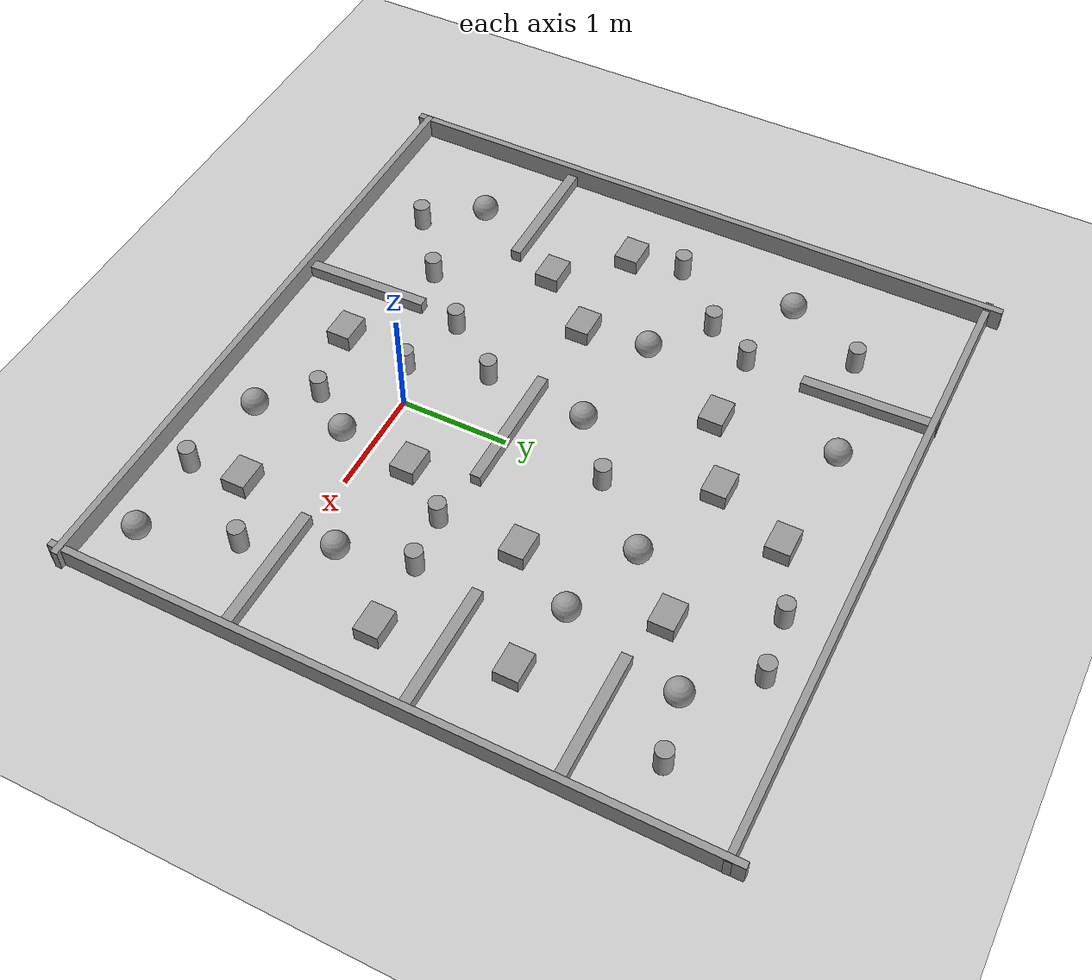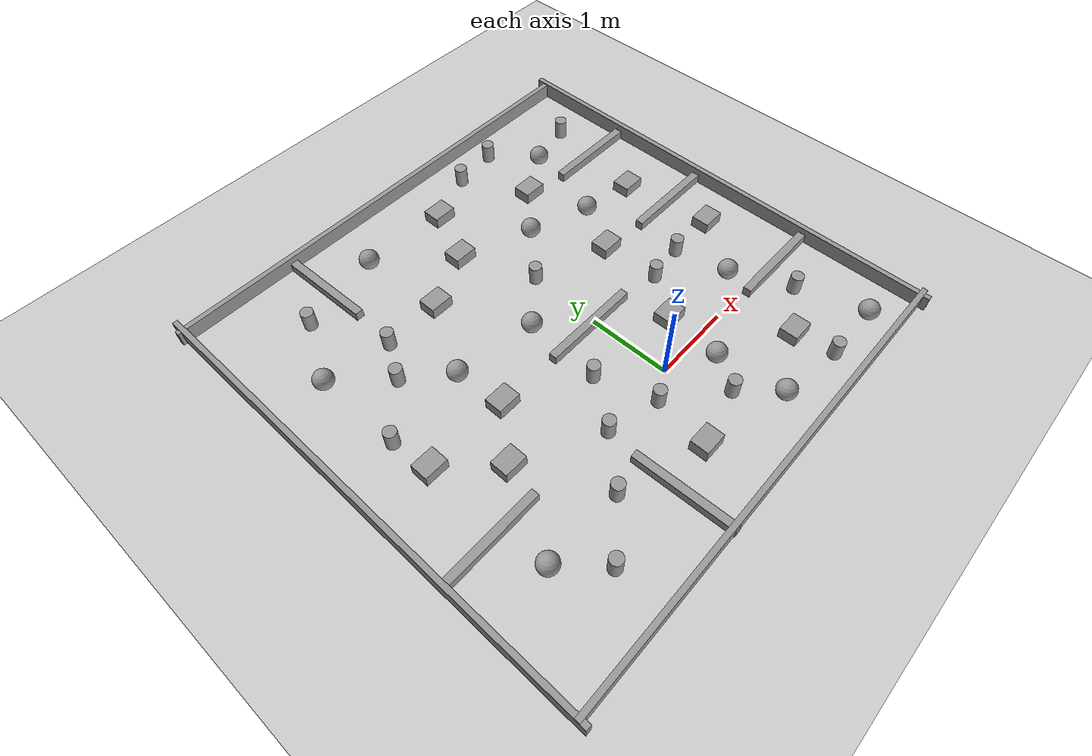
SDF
<sdf version="1.6">
 <world name="default">
  <light name="sun" type="directional">
   <pose>0 0 10 0 -0 0</pose>
   <diffuse>0.8 0.8 0.8 1</diffuse>
   <specular>0.2 0.2 0.2 1</specular>
   <attenuation>
    <range>1000</range>
    <constant>0.9</constant>
    <linear>0.01</linear>
    <quadratic>0.001</quadratic>
   </attenuation>
   <direction>-0.5 0.1 -0.9</direction>
  </light>
  <model name="ground_plane">
   <static>1</static>
   <link name="link">
    <collision name="collision">
     <geometry><plane><normal>0 0 1</normal><size>100 100</size></plane></geometry>
     <surface>
      <contact><collide_bitmask>65535</collide_bitmask></contact>
      <friction><ode><mu>100</mu><mu2>50</mu2></ode></friction>
     </surface>
    </collision>
    <visual name="visual">
     <cast_shadows>0</cast_shadows>
     <geometry><plane><normal>0 0 1</normal><size>100 100</size></plane></geometry>
     <material>
      <script><uri>file://media/materials/scripts/gazebo.material</uri><name>Gazebo/Grey</name></script>
     </material>
    </visual>
   </link>
  </model>
  <gravity>0 0 -9.8</gravity>
  <magnetic_field>6e-06 2.3e-05 -4.2e-05</magnetic_field>
  <atmosphere type="adiabatic"/>
  <physics name="default_physics" default="0" type="ode">
   <max_step_size>0.001</max_step_size>
   <real_time_factor>1</real_time_factor>
   <real_time_update_rate>1000</real_time_update_rate>
  </physics>
  <scene><ambient>0.4 0.4 0.4 1</ambient><background>0.7 0.7 0.7 1</background><shadows>1</shadows></scene>
  <audio><device>default</device></audio>
  <spherical_coordinates>
   <surface_model>EARTH_WGS84</surface_model>
   <latitude_deg>0</latitude_deg>
   <longitude_deg>0</longitude_deg>
   <elevation>0</elevation>
   <heading_deg>0</heading_deg>
  </spherical_coordinates>
  <model name="wall">
   <link name="wall::link">
    <inertial>
     <mass>1</mass>
     <inertia>
      <ixx>0.166667</ixx>
      <ixy>0</ixy>
      <ixz>0</ixz>
      <iyy>0.166667</iyy>
      <iyz>0</iyz>
      <izz>0.166667</izz>
     </inertia>
    </inertial>
    <visual name="visual">
     <geometry><box><size>6.06185 0.064282 0.203764</size></box></geometry>
     <material>
      <script><name>Gazebo/Grey</name><uri>file://media/materials/scripts/gazebo.material</uri></script>
     </material>
    </visual>
    <collision name="collision">
     <geometry><box><size>6.06185 0.064282 0.203764</size></box></geometry>
     <surface>
      <friction>
       <ode><mu>1</mu><mu2>1</mu2><fdir1>0 0 0</fdir1><slip1>0</slip1><slip2>0</slip2></ode>
       <torsional>
        <coefficient>1</coefficient>
        <patch_radius>0</patch_radius>
        <surface_radius>0</surface_radius>
        <use_patch_radius>1</use_patch_radius>
        <ode><slip>0</slip></ode>
       </torsional>
      </friction>
      <bounce><restitution_coefficient>0</restitution_coefficient><threshold>1e+06</threshold></bounce>
      <contact>
       <collide_without_contact>0</collide_without_contact>
       <collide_without_contact_bitmask>1</collide_without_contact_bitmask>
       <collide_bitmask>1</collide_bitmask>
       <ode>
        <soft_cfm>0</soft_cfm>
        <soft_erp>0.2</soft_erp>
        <kp>1e+13</kp>
        <kd>1</kd>
        <max_vel>0.01</max_vel>
        <min_depth>0</min_depth>
       </ode>
       <bullet>
        <split_impulse>1</split_impulse>
        <split_impulse_penetration_threshold>-0.01</split_impulse_penetration_threshold>
        <soft_cfm>0</soft_cfm>
        <soft_erp>0.2</soft_erp>
        <kp>1e+13</kp>
        <kd>1</kd>
       </bullet>
      </contact>
     </surface>
    </collision>
   </link>
   <static>1</static>
   <pose>-0.251992 -1.59999 0.089327 0.002776 -0.00063 0.000788</pose>
  </model>
  <model name="wall_clone">
   <link name="wall::link">
    <inertial>
     <mass>1</mass>
     <inertia>
      <ixx>0.166667</ixx>
      <ixy>0</ixy>
      <ixz>0</ixz>
      <iyy>0.166667</iyy>
      <iyz>0</iyz>
      <izz>0.166667</izz>
     </inertia>
    </inertial>
    <visual name="visual">
     <geometry><box><size>6.06185 0.064282 0.203764</size></box></geometry>
     <material>
      <script><name>Gazebo/Grey</name><uri>file://media/materials/scripts/gazebo.material</uri></script>
     </material>
    </visual>
    <collision name="collision">
     <geometry><box><size>6.06185 0.064282 0.203764</size></box></geometry>
     <surface>
      <friction>
       <ode><mu>1</mu><mu2>1</mu2><fdir1>0 0 0</fdir1><slip1>0</slip1><slip2>0</slip2></ode>
       <torsional>
        <coefficient>1</coefficient>
        <patch_radius>0</patch_radius>
        <surface_radius>0</surface_radius>
        <use_patch_radius>1</use_patch_radius>
        <ode><slip>0</slip></ode>
       </torsional>
      </friction>
      <bounce><restitution_coefficient>0</restitution_coefficient><threshold>1e+06</threshold></bounce>
      <contact>
       <collide_without_contact>0</collide_without_contact>
       <collide_without_contact_bitmask>1</collide_without_contact_bitmask>
       <collide_bitmask>1</collide_bitmask>
       <ode>
        <soft_cfm>0</soft_cfm>
        <soft_erp>0.2</soft_erp>
        <kp>1e+13</kp>
        <kd>1</kd>
        <max_vel>0.01</max_vel>
        <min_depth>0</min_depth>
       </ode>
       <bullet>
        <split_impulse>1</split_impulse>
        <split_impulse_penetration_threshold>-0.01</split_impulse_penetration_threshold>
        <soft_cfm>0</soft_cfm>
        <soft_erp>0.2</soft_erp>
        <kp>1e+13</kp>
        <kd>1</kd>
       </bullet>
      </contact>
     </surface>
    </collision>
   </link>
   <static>1</static>
   <pose>2.71395 1.32885 0.088334 -0.000616 -0.002779 1.56641</pose>
  </model>
  <model name="wall_clone_clone">
   <link name="wall::link">
    <inertial>
     <mass>1</mass>
     <inertia>
      <ixx>0.166667</ixx>
      <ixy>0</ixy>
      <ixz>0</ixz>
      <iyy>0.166667</iyy>
      <iyz>0</iyz>
      <izz>0.166667</izz>
     </inertia>
    </inertial>
    <visual name="visual">
     <geometry><box><size>6.06185 0.064282 0.203764</size></box></geometry>
     <material>
      <script><name>Gazebo/Grey</name><uri>file://media/materials/scripts/gazebo.material</uri></script>
     </material>
    </visual>
    <collision name="collision">
     <geometry><box><size>6.06185 0.064282 0.203764</size></box></geometry>
     <surface>
      <friction>
       <ode><mu>1</mu><mu2>1</mu2><fdir1>0 0 0</fdir1><slip1>0</slip1><slip2>0</slip2></ode>
       <torsional>
        <coefficient>1</coefficient>
        <patch_radius>0</patch_radius>
        <surface_radius>0</surface_radius>
        <use_patch_radius>1</use_patch_radius>
        <ode><slip>0</slip></ode>
       </torsional>
      </friction>
      <bounce><restitution_coefficient>0</restitution_coefficient><threshold>1e+06</threshold></bounce>
      <contact>
       <collide_without_contact>0</collide_without_contact>
       <collide_without_contact_bitmask>1</collide_without_contact_bitmask>
       <collide_bitmask>1</collide_bitmask>
       <ode>
        <soft_cfm>0</soft_cfm>
        <soft_erp>0.2</soft_erp>
        <kp>1e+13</kp>
        <kd>1</kd>
        <max_vel>0.01</max_vel>
        <min_depth>0</min_depth>
       </ode>
       <bullet>
        <split_impulse>1</split_impulse>
        <split_impulse_penetration_threshold>-0.01</split_impulse_penetration_threshold>
        <soft_cfm>0</soft_cfm>
        <soft_erp>0.2</soft_erp>
        <kp>1e+13</kp>
        <kd>1</kd>
       </bullet>
      </contact>
     </surface>
    </collision>
   </link>
   <static>1</static>
   <pose>-3.24153 1.32469 0.093386 -0.000616 -0.002779 1.56641</pose>
  </model>
  <model name="wall_clone_0">
   <link name="wall::link">
    <inertial>
     <mass>1</mass>
     <inertia>
      <ixx>0.166667</ixx>
      <ixy>0</ixy>
      <ixz>0</ixz>
      <iyy>0.166667</iyy>
      <iyz>0</iyz>
      <izz>0.166667</izz>
     </inertia>
    </inertial>
    <visual name="visual">
     <geometry><box><size>6.06185 0.064282 0.203764</size></box></geometry>
     <material>
      <script><name>Gazebo/Grey</name><uri>file://media/materials/scripts/gazebo.material</uri></script>
     </material>
    </visual>
    <collision name="collision">
     <geometry><box><size>6.06185 0.064282 0.203764</size></box></geometry>
     <surface>
      <friction>
       <ode><mu>1</mu><mu2>1</mu2><fdir1>0 0 0</fdir1><slip1>0</slip1><slip2>0</slip2></ode>
       <torsional>
        <coefficient>1</coefficient>
        <patch_radius>0</patch_radius>
        <surface_radius>0</surface_radius>
        <use_patch_radius>1</use_patch_radius>
        <ode><slip>0</slip></ode>
       </torsional>
      </friction>
      <bounce><restitution_coefficient>0</restitution_coefficient><threshold>1e+06</threshold></bounce>
      <contact>
       <collide_without_contact>0</collide_without_contact>
       <collide_without_contact_bitmask>1</collide_without_contact_bitmask>
       <collide_bitmask>1</collide_bitmask>
       <ode>
        <soft_cfm>0</soft_cfm>
        <soft_erp>0.2</soft_erp>
        <kp>1e+13</kp>
        <kd>1</kd>
        <max_vel>0.01</max_vel>
        <min_depth>0</min_depth>
       </ode>
       <bullet>
        <split_impulse>1</split_impulse>
        <split_impulse_penetration_threshold>-0.01</split_impulse_penetration_threshold>
        <soft_cfm>0</soft_cfm>
        <soft_erp>0.2</soft_erp>
        <kp>1e+13</kp>
        <kd>1</kd>
       </bullet>
      </contact>
     </surface>
    </collision>
   </link>
   <static>1</static>
   <pose>-0.270839 4.21948 0.083451 0.002776 -0.00063 0.000788</pose>
  </model>
  <model name="square_obstacle">
   <link name="link">
    <inertial>
     <mass>1</mass>
     <inertia>
      <ixx>0.166667</ixx>
      <ixy>0</ixy>
      <ixz>0</ixz>
      <iyy>0.166667</iyy>
      <iyz>0</iyz>
      <izz>0.166667</izz>
     </inertia>
    </inertial>
    <visual name="visual">
     <geometry><box><size>0.287479 0.224054 0.165392</size></box></geometry>
     <material>
      <script><name>Gazebo/Grey</name><uri>file://media/materials/scripts/gazebo.material</uri></script>
     </material>
    </visual>
    <collision name="collision">
     <geometry><box><size>0.287479 0.224054 0.165392</size></box></geometry>
     <surface>
      <friction>
       <ode><mu>1</mu><mu2>1</mu2><fdir1>0 0 0</fdir1><slip1>0</slip1><slip2>0</slip2></ode>
       <torsional>
        <coefficient>1</coefficient>
        <patch_radius>0</patch_radius>
        <surface_radius>0</surface_radius>
        <use_patch_radius>1</use_patch_radius>
        <ode><slip>0</slip></ode>
       </torsional>
      </friction>
      <bounce><restitution_coefficient>0</restitution_coefficient><threshold>1e+06</threshold></bounce>
      <contact>
       <collide_without_contact>0</collide_without_contact>
       <collide_without_contact_bitmask>1</collide_without_contact_bitmask>
       <collide_bitmask>1</collide_bitmask>
       <ode>
        <soft_cfm>0</soft_cfm>
        <soft_erp>0.2</soft_erp>
        <kp>1e+13</kp>
        <kd>1</kd>
        <max_vel>0.01</max_vel>
        <min_depth>0</min_depth>
       </ode>
       <bullet>
        <split_impulse>1</split_impulse>
        <split_impulse_penetration_threshold>-0.01</split_impulse_penetration_threshold>
        <soft_cfm>0</soft_cfm>
        <soft_erp>0.2</soft_erp>
        <kp>1e+13</kp>
        <kd>1</kd>
       </bullet>
      </contact>
     </surface>
    </collision>
   </link>
   <static>1</static>
   <pose>-0.448802 -0.865107 0.069671 0 -0 0</pose>
  </model>
  <model name="square_obstacle_clone_3">
   <link name="link">
    <inertial>
     <mass>1</mass>
     <inertia>
      <ixx>0.166667</ixx>
      <ixy>0</ixy>
      <ixz>0</ixz>
      <iyy>0.166667</iyy>
      <iyz>0</iyz>
      <izz>0.166667</izz>
     </inertia>
    </inertial>
    <visual name="visual">
     <geometry><box><size>0.287479 0.224054 0.165392</size></box></geometry>
     <material>
      <script><name>Gazebo/Grey</name><uri>file://media/materials/scripts/gazebo.material</uri></script>
     </material>
    </visual>
    <collision name="collision">
     <geometry><box><size>0.287479 0.224054 0.165392</size></box></geometry>
     <surface>
      <friction>
       <ode><mu>1</mu><mu2>1</mu2><fdir1>0 0 0</fdir1><slip1>0</slip1><slip2>0</slip2></ode>
       <torsional>
        <coefficient>1</coefficient>
        <patch_radius>0</patch_radius>
        <surface_radius>0</surface_radius>
        <use_patch_radius>1</use_patch_radius>
        <ode><slip>0</slip></ode>
       </torsional>
      </friction>
      <bounce><restitution_coefficient>0</restitution_coefficient><threshold>1e+06</threshold></bounce>
      <contact>
       <collide_without_contact>0</collide_without_contact>
       <collide_without_contact_bitmask>1</collide_without_contact_bitmask>
       <collide_bitmask>1</collide_bitmask>
       <ode>
        <soft_cfm>0</soft_cfm>
        <soft_erp>0.2</soft_erp>
        <kp>1e+13</kp>
        <kd>1</kd>
        <max_vel>0.01</max_vel>
        <min_depth>0</min_depth>
       </ode>
       <bullet>
        <split_impulse>1</split_impulse>
        <split_impulse_penetration_threshold>-0.01</split_impulse_penetration_threshold>
        <soft_cfm>0</soft_cfm>
        <soft_erp>0.2</soft_erp>
        <kp>1e+13</kp>
        <kd>1</kd>
       </bullet>
      </contact>
     </surface>
    </collision>
   </link>
   <static>1</static>
   <pose>1.97683 2.12663 0.043093 0 -0 0</pose>
  </model>
  <model name="square_obstacle_clone_4">
   <link name="link">
    <inertial>
     <mass>1</mass>
     <inertia>
      <ixx>0.166667</ixx>
      <ixy>0</ixy>
      <ixz>0</ixz>
      <iyy>0.166667</iyy>
      <iyz>0</iyz>
      <izz>0.166667</izz>
     </inertia>
    </inertial>
    <visual name="visual">
     <geometry><box><size>0.287479 0.224054 0.165392</size></box></geometry>
     <material>
      <script><name>Gazebo/Grey</name><uri>file://media/materials/scripts/gazebo.material</uri></script>
     </material>
    </visual>
    <collision name="collision">
     <geometry><box><size>0.287479 0.224054 0.165392</size></box></geometry>
     <surface>
      <friction>
       <ode><mu>1</mu><mu2>1</mu2><fdir1>0 0 0</fdir1><slip1>0</slip1><slip2>0</slip2></ode>
       <torsional>
        <coefficient>1</coefficient>
        <patch_radius>0</patch_radius>
        <surface_radius>0</surface_radius>
        <use_patch_radius>1</use_patch_radius>
        <ode><slip>0</slip></ode>
       </torsional>
      </friction>
      <bounce><restitution_coefficient>0</restitution_coefficient><threshold>1e+06</threshold></bounce>
      <contact>
       <collide_without_contact>0</collide_without_contact>
       <collide_without_contact_bitmask>1</collide_without_contact_bitmask>
       <collide_bitmask>1</collide_bitmask>
       <ode>
        <soft_cfm>0</soft_cfm>
        <soft_erp>0.2</soft_erp>
        <kp>1e+13</kp>
        <kd>1</kd>
        <max_vel>0.01</max_vel>
        <min_depth>0</min_depth>
       </ode>
       <bullet>
        <split_impulse>1</split_impulse>
        <split_impulse_penetration_threshold>-0.01</split_impulse_penetration_threshold>
        <soft_cfm>0</soft_cfm>
        <soft_erp>0.2</soft_erp>
        <kp>1e+13</kp>
        <kd>1</kd>
       </bullet>
      </contact>
     </surface>
    </collision>
   </link>
   <static>1</static>
   <pose>1.37279 -0.76147 0.055043 0 -0 0</pose>
  </model>
  <model name="sphere_obstacles_clone_2">
   <link name="sphere_obstacles_clone_2::link">
    <inertial>
     <mass>1</mass>
     <inertia><ixx>0.1</ixx><ixy>0</ixy><ixz>0</ixz><iyy>0.1</iyy><iyz>0</iyz><izz>0.1</izz></inertia>
    </inertial>
    <visual name="visual">
     <geometry><sphere><radius>0.121078</radius></sphere></geometry>
     <material>
      <script><name>Gazebo/Grey</name><uri>file://media/materials/scripts/gazebo.material</uri></script>
     </material>
    </visual>
    <collision name="collision">
     <geometry><sphere><radius>0.121078</radius></sphere></geometry>
     <surface>
      <friction>
       <ode><mu>1</mu><mu2>1</mu2><fdir1>0 0 0</fdir1><slip1>0</slip1><slip2>0</slip2></ode>
       <torsional>
        <coefficient>1</coefficient>
        <patch_radius>0</patch_radius>
        <surface_radius>0</surface_radius>
        <use_patch_radius>1</use_patch_radius>
        <ode><slip>0</slip></ode>
       </torsional>
      </friction>
      <bounce><restitution_coefficient>0</restitution_coefficient><threshold>1e+06</threshold></bounce>
      <contact>
       <collide_without_contact>0</collide_without_contact>
       <collide_without_contact_bitmask>1</collide_without_contact_bitmask>
       <collide_bitmask>1</collide_bitmask>
       <ode>
        <soft_cfm>0</soft_cfm>
        <soft_erp>0.2</soft_erp>
        <kp>1e+13</kp>
        <kd>1</kd>
        <max_vel>0.01</max_vel>
        <min_depth>0</min_depth>
       </ode>
       <bullet>
        <split_impulse>1</split_impulse>
        <split_impulse_penetration_threshold>-0.01</split_impulse_penetration_threshold>
        <soft_cfm>0</soft_cfm>
        <soft_erp>0.2</soft_erp>
        <kp>1e+13</kp>
        <kd>1</kd>
       </bullet>
      </contact>
     </surface>
    </collision>
   </link>
   <static>1</static>
   <pose>1.62312 0.3049 0.0728 0 -0 0</pose>
  </model>
  <model name="square_obstacle_clone_4_clone">
   <link name="link">
    <inertial>
     <mass>1</mass>
     <inertia>
      <ixx>0.166667</ixx>
      <ixy>0</ixy>
      <ixz>0</ixz>
      <iyy>0.166667</iyy>
      <iyz>0</iyz>
      <izz>0.166667</izz>
     </inertia>
    </inertial>
    <visual name="visual">
     <geometry><box><size>0.287479 0.224054 0.165392</size></box></geometry>
     <material>
      <script><name>Gazebo/Grey</name><uri>file://media/materials/scripts/gazebo.material</uri></script>
     </material>
    </visual>
    <collision name="collision">
     <geometry><box><size>0.287479 0.224054 0.165392</size></box></geometry>
     <surface>
      <friction>
       <ode><mu>1</mu><mu2>1</mu2><fdir1>0 0 0</fdir1><slip1>0</slip1><slip2>0</slip2></ode>
       <torsional>
        <coefficient>1</coefficient>
        <patch_radius>0</patch_radius>
        <surface_radius>0</surface_radius>
        <use_patch_radius>1</use_patch_radius>
        <ode><slip>0</slip></ode>
       </torsional>
      </friction>
      <bounce><restitution_coefficient>0</restitution_coefficient><threshold>1e+06</threshold></bounce>
      <contact>
       <collide_without_contact>0</collide_without_contact>
       <collide_without_contact_bitmask>1</collide_without_contact_bitmask>
       <collide_bitmask>1</collide_bitmask>
       <ode>
        <soft_cfm>0</soft_cfm>
        <soft_erp>0.2</soft_erp>
        <kp>1e+13</kp>
        <kd>1</kd>
        <max_vel>0.01</max_vel>
        <min_depth>0</min_depth>
       </ode>
       <bullet>
        <split_impulse>1</split_impulse>
        <split_impulse_penetration_threshold>-0.01</split_impulse_penetration_threshold>
        <soft_cfm>0</soft_cfm>
        <soft_erp>0.2</soft_erp>
        <kp>1e+13</kp>
        <kd>1</kd>
       </bullet>
      </contact>
     </surface>
    </collision>
   </link>
   <static>1</static>
   <pose>0.9652 1.63657 0.055043 0 -0 0</pose>
  </model>
  <model name="square_obstacle_clone_4_clone_0">
   <link name="link">
    <inertial>
     <mass>1</mass>
     <inertia>
      <ixx>0.166667</ixx>
      <ixy>0</ixy>
      <ixz>0</ixz>
      <iyy>0.166667</iyy>
      <iyz>0</iyz>
      <izz>0.166667</izz>
     </inertia>
    </inertial>
    <visual name="visual">
     <geometry><box><size>0.287479 0.224054 0.165392</size></box></geometry>
     <material>
      <script><name>Gazebo/Grey</name><uri>file://media/materials/scripts/gazebo.material</uri></script>
     </material>
    </visual>
    <collision name="collision">
     <geometry><box><size>0.287479 0.224054 0.165392</size></box></geometry>
     <surface>
      <friction>
       <ode><mu>1</mu><mu2>1</mu2><fdir1>0 0 0</fdir1><slip1>0</slip1><slip2>0</slip2></ode>
       <torsional>
        <coefficient>1</coefficient>
        <patch_radius>0</patch_radius>
        <surface_radius>0</surface_radius>
        <use_patch_radius>1</use_patch_radius>
        <ode><slip>0</slip></ode>
       </torsional>
      </friction>
      <bounce><restitution_coefficient>0</restitution_coefficient><threshold>1e+06</threshold></bounce>
      <contact>
       <collide_without_contact>0</collide_without_contact>
       <collide_without_contact_bitmask>1</collide_without_contact_bitmask>
       <collide_bitmask>1</collide_bitmask>
       <ode>
        <soft_cfm>0</soft_cfm>
        <soft_erp>0.2</soft_erp>
        <kp>1e+13</kp>
        <kd>1</kd>
        <max_vel>0.01</max_vel>
        <min_depth>0</min_depth>
       </ode>
       <bullet>
        <split_impulse>1</split_impulse>
        <split_impulse_penetration_threshold>-0.01</split_impulse_penetration_threshold>
        <soft_cfm>0</soft_cfm>
        <soft_erp>0.2</soft_erp>
        <kp>1e+13</kp>
        <kd>1</kd>
       </bullet>
      </contact>
     </surface>
    </collision>
   </link>
   <static>1</static>
   <pose>-1.04193 2.50349 0.055043 0 -0 0</pose>
  </model>
  <model name="square_obstacle_clone_4_clone_1">
   <link name="link">
    <inertial>
     <mass>1</mass>
     <inertia>
      <ixx>0.166667</ixx>
      <ixy>0</ixy>
      <ixz>0</ixz>
      <iyy>0.166667</iyy>
      <iyz>0</iyz>
      <izz>0.166667</izz>
     </inertia>
    </inertial>
    <visual name="visual">
     <geometry><box><size>0.287479 0.224054 0.165392</size></box></geometry>
     <material>
      <script><name>Gazebo/Grey</name><uri>file://media/materials/scripts/gazebo.material</uri></script>
     </material>
    </visual>
    <collision name="collision">
     <geometry><box><size>0.287479 0.224054 0.165392</size></box></geometry>
     <surface>
      <friction>
       <ode><mu>1</mu><mu2>1</mu2><fdir1>0 0 0</fdir1><slip1>0</slip1><slip2>0</slip2></ode>
       <torsional>
        <coefficient>1</coefficient>
        <patch_radius>0</patch_radius>
        <surface_radius>0</surface_radius>
        <use_patch_radius>1</use_patch_radius>
        <ode><slip>0</slip></ode>
       </torsional>
      </friction>
      <bounce><restitution_coefficient>0</restitution_coefficient><threshold>1e+06</threshold></bounce>
      <contact>
       <collide_without_contact>0</collide_without_contact>
       <collide_without_contact_bitmask>1</collide_without_contact_bitmask>
       <collide_bitmask>1</collide_bitmask>
       <ode>
        <soft_cfm>0</soft_cfm>
        <soft_erp>0.2</soft_erp>
        <kp>1e+13</kp>
        <kd>1</kd>
        <max_vel>0.01</max_vel>
        <min_depth>0</min_depth>
       </ode>
       <bullet>
        <split_impulse>1</split_impulse>
        <split_impulse_penetration_threshold>-0.01</split_impulse_penetration_threshold>
        <soft_cfm>0</soft_cfm>
        <soft_erp>0.2</soft_erp>
        <kp>1e+13</kp>
        <kd>1</kd>
       </bullet>
      </contact>
     </surface>
    </collision>
   </link>
   <static>1</static>
   <pose>-1.95288 0.456535 0.055043 0 -0 0</pose>
  </model>
  <model name="square_obstacle_clone_4_clone_2">
   <link name="link">
    <inertial>
     <mass>1</mass>
     <inertia>
      <ixx>0.166667</ixx>
      <ixy>0</ixy>
      <ixz>0</ixz>
      <iyy>0.166667</iyy>
      <iyz>0</iyz>
      <izz>0.166667</izz>
     </inertia>
    </inertial>
    <visual name="visual">
     <geometry><box><size>0.287479 0.224054 0.165392</size></box></geometry>
     <material>
      <script><name>Gazebo/Grey</name><uri>file://media/materials/scripts/gazebo.material</uri></script>
     </material>
    </visual>
    <collision name="collision">
     <geometry><box><size>0.287479 0.224054 0.165392</size></box></geometry>
     <surface>
      <friction>
       <ode><mu>1</mu><mu2>1</mu2><fdir1>0 0 0</fdir1><slip1>0</slip1><slip2>0</slip2></ode>
       <torsional>
        <coefficient>1</coefficient>
        <patch_radius>0</patch_radius>
        <surface_radius>0</surface_radius>
        <use_patch_radius>1</use_patch_radius>
        <ode><slip>0</slip></ode>
       </torsional>
      </friction>
      <bounce><restitution_coefficient>0</restitution_coefficient><threshold>1e+06</threshold></bounce>
      <contact>
       <collide_without_contact>0</collide_without_contact>
       <collide_without_contact_bitmask>1</collide_without_contact_bitmask>
       <collide_bitmask>1</collide_bitmask>
       <ode>
        <soft_cfm>0</soft_cfm>
        <soft_erp>0.2</soft_erp>
        <kp>1e+13</kp>
        <kd>1</kd>
        <max_vel>0.01</max_vel>
        <min_depth>0</min_depth>
       </ode>
       <bullet>
        <split_impulse>1</split_impulse>
        <split_impulse_penetration_threshold>-0.01</split_impulse_penetration_threshold>
        <soft_cfm>0</soft_cfm>
        <soft_erp>0.2</soft_erp>
        <kp>1e+13</kp>
        <kd>1</kd>
       </bullet>
      </contact>
     </surface>
    </collision>
   </link>
   <static>1</static>
   <pose>-0.036173 3.52521 0.055043 0 -0 0</pose>
  </model>
  <model name="sphere_obstacles_clone_2_clone">
   <link name="sphere_obstacles_clone_2::link">
    <inertial>
     <mass>1</mass>
     <inertia><ixx>0.1</ixx><ixy>0</ixy><ixz>0</ixz><iyy>0.1</iyy><iyz>0</iyz><izz>0.1</izz></inertia>
    </inertial>
    <visual name="visual">
     <geometry><sphere><radius>0.121078</radius></sphere></geometry>
     <material>
      <script><name>Gazebo/Grey</name><uri>file://media/materials/scripts/gazebo.material</uri></script>
     </material>
    </visual>
    <collision name="collision">
     <geometry><sphere><radius>0.121078</radius></sphere></geometry>
     <surface>
      <friction>
       <ode><mu>1</mu><mu2>1</mu2><fdir1>0 0 0</fdir1><slip1>0</slip1><slip2>0</slip2></ode>
       <torsional>
        <coefficient>1</coefficient>
        <patch_radius>0</patch_radius>
        <surface_radius>0</surface_radius>
        <use_patch_radius>1</use_patch_radius>
        <ode><slip>0</slip></ode>
       </torsional>
      </friction>
      <bounce><restitution_coefficient>0</restitution_coefficient><threshold>1e+06</threshold></bounce>
      <contact>
       <collide_without_contact>0</collide_without_contact>
       <collide_without_contact_bitmask>1</collide_without_contact_bitmask>
       <collide_bitmask>1</collide_bitmask>
       <ode>
        <soft_cfm>0</soft_cfm>
        <soft_erp>0.2</soft_erp>
        <kp>1e+13</kp>
        <kd>1</kd>
        <max_vel>0.01</max_vel>
        <min_depth>0</min_depth>
       </ode>
       <bullet>
        <split_impulse>1</split_impulse>
        <split_impulse_penetration_threshold>-0.01</split_impulse_penetration_threshold>
        <soft_cfm>0</soft_cfm>
        <soft_erp>0.2</soft_erp>
        <kp>1e+13</kp>
        <kd>1</kd>
       </bullet>
      </contact>
     </surface>
    </collision>
   </link>
   <static>1</static>
   <pose>-0.518676 1.4857 0.0728 0 -0 0</pose>
  </model>
  <model name="sphere_obstacles_clone_2_clone_0">
   <link name="sphere_obstacles_clone_2::link">
    <inertial>
     <mass>1</mass>
     <inertia><ixx>0.1</ixx><ixy>0</ixy><ixz>0</ixz><iyy>0.1</iyy><iyz>0</iyz><izz>0.1</izz></inertia>
    </inertial>
    <visual name="visual">
     <geometry><sphere><radius>0.121078</radius></sphere></geometry>
     <material>
      <script><name>Gazebo/Grey</name><uri>file://media/materials/scripts/gazebo.material</uri></script>
     </material>
    </visual>
    <collision name="collision">
     <geometry><sphere><radius>0.121078</radius></sphere></geometry>
     <surface>
      <friction>
       <ode><mu>1</mu><mu2>1</mu2><fdir1>0 0 0</fdir1><slip1>0</slip1><slip2>0</slip2></ode>
       <torsional>
        <coefficient>1</coefficient>
        <patch_radius>0</patch_radius>
        <surface_radius>0</surface_radius>
        <use_patch_radius>1</use_patch_radius>
        <ode><slip>0</slip></ode>
       </torsional>
      </friction>
      <bounce><restitution_coefficient>0</restitution_coefficient><threshold>1e+06</threshold></bounce>
      <contact>
       <collide_without_contact>0</collide_without_contact>
       <collide_without_contact_bitmask>1</collide_without_contact_bitmask>
       <collide_bitmask>1</collide_bitmask>
       <ode>
        <soft_cfm>0</soft_cfm>
        <soft_erp>0.2</soft_erp>
        <kp>1e+13</kp>
        <kd>1</kd>
        <max_vel>0.01</max_vel>
        <min_depth>0</min_depth>
       </ode>
       <bullet>
        <split_impulse>1</split_impulse>
        <split_impulse_penetration_threshold>-0.01</split_impulse_penetration_threshold>
        <soft_cfm>0</soft_cfm>
        <soft_erp>0.2</soft_erp>
        <kp>1e+13</kp>
        <kd>1</kd>
       </bullet>
      </contact>
     </surface>
    </collision>
   </link>
   <static>1</static>
   <pose>-2.56968 2.61576 0.0728 0 -0 0</pose>
  </model>
  <model name="sphere_obstacles_clone_2_clone_1">
   <link name="sphere_obstacles_clone_2::link">
    <inertial>
     <mass>1</mass>
     <inertia><ixx>0.1</ixx><ixy>0</ixy><ixz>0</ixz><iyy>0.1</iyy><iyz>0</iyz><izz>0.1</izz></inertia>
    </inertial>
    <visual name="visual">
     <geometry><sphere><radius>0.121078</radius></sphere></geometry>
     <material>
      <script><name>Gazebo/Grey</name><uri>file://media/materials/scripts/gazebo.material</uri></script>
     </material>
    </visual>
    <collision name="collision">
     <geometry><sphere><radius>0.121078</radius></sphere></geometry>
     <surface>
      <friction>
       <ode><mu>1</mu><mu2>1</mu2><fdir1>0 0 0</fdir1><slip1>0</slip1><slip2>0</slip2></ode>
       <torsional>
        <coefficient>1</coefficient>
        <patch_radius>0</patch_radius>
        <surface_radius>0</surface_radius>
        <use_patch_radius>1</use_patch_radius>
        <ode><slip>0</slip></ode>
       </torsional>
      </friction>
      <bounce><restitution_coefficient>0</restitution_coefficient><threshold>1e+06</threshold></bounce>
      <contact>
       <collide_without_contact>0</collide_without_contact>
       <collide_without_contact_bitmask>1</collide_without_contact_bitmask>
       <collide_bitmask>1</collide_bitmask>
       <ode>
        <soft_cfm>0</soft_cfm>
        <soft_erp>0.2</soft_erp>
        <kp>1e+13</kp>
        <kd>1</kd>
        <max_vel>0.01</max_vel>
        <min_depth>0</min_depth>
       </ode>
       <bullet>
        <split_impulse>1</split_impulse>
        <split_impulse_penetration_threshold>-0.01</split_impulse_penetration_threshold>
        <soft_cfm>0</soft_cfm>
        <soft_erp>0.2</soft_erp>
        <kp>1e+13</kp>
        <kd>1</kd>
       </bullet>
      </contact>
     </surface>
    </collision>
   </link>
   <static>1</static>
   <pose>1.60832 3.34503 0.0728 0 -0 0</pose>
  </model>
  <model name="sphere_obstacles_clone_2_clone_2">
   <link name="sphere_obstacles_clone_2::link">
    <inertial>
     <mass>1</mass>
     <inertia><ixx>0.1</ixx><ixy>0</ixy><ixz>0</ixz><iyy>0.1</iyy><iyz>0</iyz><izz>0.1</izz></inertia>
    </inertial>
    <visual name="visual">
     <geometry><sphere><radius>0.121078</radius></sphere></geometry>
     <material>
      <script><name>Gazebo/Grey</name><uri>file://media/materials/scripts/gazebo.material</uri></script>
     </material>
    </visual>
    <collision name="collision">
     <geometry><sphere><radius>0.121078</radius></sphere></geometry>
     <surface>
      <friction>
       <ode><mu>1</mu><mu2>1</mu2><fdir1>0 0 0</fdir1><slip1>0</slip1><slip2>0</slip2></ode>
       <torsional>
        <coefficient>1</coefficient>
        <patch_radius>0</patch_radius>
        <surface_radius>0</surface_radius>
        <use_patch_radius>1</use_patch_radius>
        <ode><slip>0</slip></ode>
       </torsional>
      </friction>
      <bounce><restitution_coefficient>0</restitution_coefficient><threshold>1e+06</threshold></bounce>
      <contact>
       <collide_without_contact>0</collide_without_contact>
       <collide_without_contact_bitmask>1</collide_without_contact_bitmask>
       <collide_bitmask>1</collide_bitmask>
       <ode>
        <soft_cfm>0</soft_cfm>
        <soft_erp>0.2</soft_erp>
        <kp>1e+13</kp>
        <kd>1</kd>
        <max_vel>0.01</max_vel>
        <min_depth>0</min_depth>
       </ode>
       <bullet>
        <split_impulse>1</split_impulse>
        <split_impulse_penetration_threshold>-0.01</split_impulse_penetration_threshold>
        <soft_cfm>0</soft_cfm>
        <soft_erp>0.2</soft_erp>
        <kp>1e+13</kp>
        <kd>1</kd>
       </bullet>
      </contact>
     </surface>
    </collision>
   </link>
   <static>1</static>
   <pose>0.551876 2.50628 0.0728 0 -0 0</pose>
  </model>
  <model name="sphere_obstacles_clone_2_clone_3">
   <link name="sphere_obstacles_clone_2::link">
    <inertial>
     <mass>1</mass>
     <inertia><ixx>0.1</ixx><ixy>0</ixy><ixz>0</ixz><iyy>0.1</iyy><iyz>0</iyz><izz>0.1</izz></inertia>
    </inertial>
    <visual name="visual">
     <geometry><sphere><radius>0.121078</radius></sphere></geometry>
     <material>
      <script><name>Gazebo/Grey</name><uri>file://media/materials/scripts/gazebo.material</uri></script>
     </material>
    </visual>
    <collision name="collision">
     <geometry><sphere><radius>0.121078</radius></sphere></geometry>
     <surface>
      <friction>
       <ode><mu>1</mu><mu2>1</mu2><fdir1>0 0 0</fdir1><slip1>0</slip1><slip2>0</slip2></ode>
       <torsional>
        <coefficient>1</coefficient>
        <patch_radius>0</patch_radius>
        <surface_radius>0</surface_radius>
        <use_patch_radius>1</use_patch_radius>
        <ode><slip>0</slip></ode>
       </torsional>
      </friction>
      <bounce><restitution_coefficient>0</restitution_coefficient><threshold>1e+06</threshold></bounce>
      <contact>
       <collide_without_contact>0</collide_without_contact>
       <collide_without_contact_bitmask>1</collide_without_contact_bitmask>
       <collide_bitmask>1</collide_bitmask>
       <ode>
        <soft_cfm>0</soft_cfm>
        <soft_erp>0.2</soft_erp>
        <kp>1e+13</kp>
        <kd>1</kd>
        <max_vel>0.01</max_vel>
        <min_depth>0</min_depth>
       </ode>
       <bullet>
        <split_impulse>1</split_impulse>
        <split_impulse_penetration_threshold>-0.01</split_impulse_penetration_threshold>
        <soft_cfm>0</soft_cfm>
        <soft_erp>0.2</soft_erp>
        <kp>1e+13</kp>
        <kd>1</kd>
       </bullet>
      </contact>
     </surface>
    </collision>
   </link>
   <static>1</static>
   <pose>0.539291 -0.300448 0.0728 0 -0 0</pose>
  </model>
  <model name="sphere_obstacles_clone_2_clone_4">
   <link name="sphere_obstacles_clone_2::link">
    <inertial>
     <mass>1</mass>
     <inertia><ixx>0.1</ixx><ixy>0</ixy><ixz>0</ixz><iyy>0.1</iyy><iyz>0</iyz><izz>0.1</izz></inertia>
    </inertial>
    <visual name="visual">
     <geometry><sphere><radius>0.121078</radius></sphere></geometry>
     <material>
      <script><name>Gazebo/Grey</name><uri>file://media/materials/scripts/gazebo.material</uri></script>
     </material>
    </visual>
    <collision name="collision">
     <geometry><sphere><radius>0.121078</radius></sphere></geometry>
     <surface>
      <friction>
       <ode><mu>1</mu><mu2>1</mu2><fdir1>0 0 0</fdir1><slip1>0</slip1><slip2>0</slip2></ode>
       <torsional>
        <coefficient>1</coefficient>
        <patch_radius>0</patch_radius>
        <surface_radius>0</surface_radius>
        <use_patch_radius>1</use_patch_radius>
        <ode><slip>0</slip></ode>
       </torsional>
      </friction>
      <bounce><restitution_coefficient>0</restitution_coefficient><threshold>1e+06</threshold></bounce>
      <contact>
       <collide_without_contact>0</collide_without_contact>
       <collide_without_contact_bitmask>1</collide_without_contact_bitmask>
       <collide_bitmask>1</collide_bitmask>
       <ode>
        <soft_cfm>0</soft_cfm>
        <soft_erp>0.2</soft_erp>
        <kp>1e+13</kp>
        <kd>1</kd>
        <max_vel>0.01</max_vel>
        <min_depth>0</min_depth>
       </ode>
       <bullet>
        <split_impulse>1</split_impulse>
        <split_impulse_penetration_threshold>-0.01</split_impulse_penetration_threshold>
        <soft_cfm>0</soft_cfm>
        <soft_erp>0.2</soft_erp>
        <kp>1e+13</kp>
        <kd>1</kd>
       </bullet>
      </contact>
     </surface>
    </collision>
   </link>
   <static>1</static>
   <pose>-2.4503 -0.52455 0.0728 0 -0 0</pose>
  </model>
  <model name="sphere_obstacles_clone_2_clone_5">
   <link name="sphere_obstacles_clone_2::link">
    <inertial>
     <mass>1</mass>
     <inertia><ixx>0.1</ixx><ixy>0</ixy><ixz>0</ixz><iyy>0.1</iyy><iyz>0</iyz><izz>0.1</izz></inertia>
    </inertial>
    <visual name="visual">
     <geometry><sphere><radius>0.121078</radius></sphere></geometry>
     <material>
      <script><name>Gazebo/Grey</name><uri>file://media/materials/scripts/gazebo.material</uri></script>
     </material>
    </visual>
    <collision name="collision">
     <geometry><sphere><radius>0.121078</radius></sphere></geometry>
     <surface>
      <friction>
       <ode><mu>1</mu><mu2>1</mu2><fdir1>0 0 0</fdir1><slip1>0</slip1><slip2>0</slip2></ode>
       <torsional>
        <coefficient>1</coefficient>
        <patch_radius>0</patch_radius>
        <surface_radius>0</surface_radius>
        <use_patch_radius>1</use_patch_radius>
        <ode><slip>0</slip></ode>
       </torsional>
      </friction>
      <bounce><restitution_coefficient>0</restitution_coefficient><threshold>1e+06</threshold></bounce>
      <contact>
       <collide_without_contact>0</collide_without_contact>
       <collide_without_contact_bitmask>1</collide_without_contact_bitmask>
       <collide_bitmask>1</collide_bitmask>
       <ode>
        <soft_cfm>0</soft_cfm>
        <soft_erp>0.2</soft_erp>
        <kp>1e+13</kp>
        <kd>1</kd>
        <max_vel>0.01</max_vel>
        <min_depth>0</min_depth>
       </ode>
       <bullet>
        <split_impulse>1</split_impulse>
        <split_impulse_penetration_threshold>-0.01</split_impulse_penetration_threshold>
        <soft_cfm>0</soft_cfm>
        <soft_erp>0.2</soft_erp>
        <kp>1e+13</kp>
        <kd>1</kd>
       </bullet>
      </contact>
     </surface>
    </collision>
   </link>
   <static>1</static>
   <pose>2.19214 -1.24737 0.0728 0 -0 0</pose>
  </model>
  <model name="sphere_obstacles_clone_2_clone_clone">
   <link name="sphere_obstacles_clone_2::link">
    <inertial>
     <mass>1</mass>
     <inertia><ixx>0.1</ixx><ixy>0</ixy><ixz>0</ixz><iyy>0.1</iyy><iyz>0</iyz><izz>0.1</izz></inertia>
    </inertial>
    <visual name="visual">
     <geometry><sphere><radius>0.121078</radius></sphere></geometry>
     <material>
      <script><name>Gazebo/Grey</name><uri>file://media/materials/scripts/gazebo.material</uri></script>
     </material>
    </visual>
    <collision name="collision">
     <geometry><sphere><radius>0.121078</radius></sphere></geometry>
     <surface>
      <friction>
       <ode><mu>1</mu><mu2>1</mu2><fdir1>0 0 0</fdir1><slip1>0</slip1><slip2>0</slip2></ode>
       <torsional>
        <coefficient>1</coefficient>
        <patch_radius>0</patch_radius>
        <surface_radius>0</surface_radius>
        <use_patch_radius>1</use_patch_radius>
        <ode><slip>0</slip></ode>
       </torsional>
      </friction>
      <bounce><restitution_coefficient>0</restitution_coefficient><threshold>1e+06</threshold></bounce>
      <contact>
       <collide_without_contact>0</collide_without_contact>
       <collide_without_contact_bitmask>1</collide_without_contact_bitmask>
       <collide_bitmask>1</collide_bitmask>
       <ode>
        <soft_cfm>0</soft_cfm>
        <soft_erp>0.2</soft_erp>
        <kp>1e+13</kp>
        <kd>1</kd>
        <max_vel>0.01</max_vel>
        <min_depth>0</min_depth>
       </ode>
       <bullet>
        <split_impulse>1</split_impulse>
        <split_impulse_penetration_threshold>-0.01</split_impulse_penetration_threshold>
        <soft_cfm>0</soft_cfm>
        <soft_erp>0.2</soft_erp>
        <kp>1e+13</kp>
        <kd>1</kd>
       </bullet>
      </contact>
     </surface>
    </collision>
   </link>
   <static>1</static>
   <pose>-1.12901 3.58744 0.0728 0 -0 0</pose>
  </model>
  <model name="square_obstacle_clone_4_clone_clone">
   <link name="link">
    <inertial>
     <mass>1</mass>
     <inertia>
      <ixx>0.166667</ixx>
      <ixy>0</ixy>
      <ixz>0</ixz>
      <iyy>0.166667</iyy>
      <iyz>0</iyz>
      <izz>0.166667</izz>
     </inertia>
    </inertial>
    <visual name="visual">
     <geometry><box><size>0.287479 0.224054 0.165392</size></box></geometry>
     <material>
      <script><name>Gazebo/Grey</name><uri>file://media/materials/scripts/gazebo.material</uri></script>
     </material>
    </visual>
    <collision name="collision">
     <geometry><box><size>0.287479 0.224054 0.165392</size></box></geometry>
     <surface>
      <friction>
       <ode><mu>1</mu><mu2>1</mu2><fdir1>0 0 0</fdir1><slip1>0</slip1><slip2>0</slip2></ode>
       <torsional>
        <coefficient>1</coefficient>
        <patch_radius>0</patch_radius>
        <surface_radius>0</surface_radius>
        <use_patch_radius>1</use_patch_radius>
        <ode><slip>0</slip></ode>
       </torsional>
      </friction>
      <bounce><restitution_coefficient>0</restitution_coefficient><threshold>1e+06</threshold></bounce>
      <contact>
       <collide_without_contact>0</collide_without_contact>
       <collide_without_contact_bitmask>1</collide_without_contact_bitmask>
       <collide_bitmask>1</collide_bitmask>
       <ode>
        <soft_cfm>0</soft_cfm>
        <soft_erp>0.2</soft_erp>
        <kp>1e+13</kp>
        <kd>1</kd>
        <max_vel>0.01</max_vel>
        <min_depth>0</min_depth>
       </ode>
       <bullet>
        <split_impulse>1</split_impulse>
        <split_impulse_penetration_threshold>-0.01</split_impulse_penetration_threshold>
        <soft_cfm>0</soft_cfm>
        <soft_erp>0.2</soft_erp>
        <kp>1e+13</kp>
        <kd>1</kd>
       </bullet>
      </contact>
     </surface>
    </collision>
   </link>
   <static>1</static>
   <pose>1.03503 2.98935 0.055043 0 -0 0</pose>
  </model>
  <model name="square_obstacle_clone_4_clone_clone_0">
   <link name="link">
    <inertial>
     <mass>1</mass>
     <inertia>
      <ixx>0.166667</ixx>
      <ixy>0</ixy>
      <ixz>0</ixz>
      <iyy>0.166667</iyy>
      <iyz>0</iyz>
      <izz>0.166667</izz>
     </inertia>
    </inertial>
    <visual name="visual">
     <geometry><box><size>0.287479 0.224054 0.165392</size></box></geometry>
     <material>
      <script><name>Gazebo/Grey</name><uri>file://media/materials/scripts/gazebo.material</uri></script>
     </material>
    </visual>
    <collision name="collision">
     <geometry><box><size>0.287479 0.224054 0.165392</size></box></geometry>
     <surface>
      <friction>
       <ode><mu>1</mu><mu2>1</mu2><fdir1>0 0 0</fdir1><slip1>0</slip1><slip2>0</slip2></ode>
       <torsional>
        <coefficient>1</coefficient>
        <patch_radius>0</patch_radius>
        <surface_radius>0</surface_radius>
        <use_patch_radius>1</use_patch_radius>
        <ode><slip>0</slip></ode>
       </torsional>
      </friction>
      <bounce><restitution_coefficient>0</restitution_coefficient><threshold>1e+06</threshold></bounce>
      <contact>
       <collide_without_contact>0</collide_without_contact>
       <collide_without_contact_bitmask>1</collide_without_contact_bitmask>
       <collide_bitmask>1</collide_bitmask>
       <ode>
        <soft_cfm>0</soft_cfm>
        <soft_erp>0.2</soft_erp>
        <kp>1e+13</kp>
        <kd>1</kd>
        <max_vel>0.01</max_vel>
        <min_depth>0</min_depth>
       </ode>
       <bullet>
        <split_impulse>1</split_impulse>
        <split_impulse_penetration_threshold>-0.01</split_impulse_penetration_threshold>
        <soft_cfm>0</soft_cfm>
        <soft_erp>0.2</soft_erp>
        <kp>1e+13</kp>
        <kd>1</kd>
       </bullet>
      </contact>
     </surface>
    </collision>
   </link>
   <static>1</static>
   <pose>-1.47571 1.0085 0.055043 0 -0 0</pose>
  </model>
  <model name="square_obstacle_clone_4_clone_clone_1">
   <link name="link">
    <inertial>
     <mass>1</mass>
     <inertia>
      <ixx>0.166667</ixx>
      <ixy>0</ixy>
      <ixz>0</ixz>
      <iyy>0.166667</iyy>
      <iyz>0</iyz>
      <izz>0.166667</izz>
     </inertia>
    </inertial>
    <visual name="visual">
     <geometry><box><size>0.287479 0.224054 0.165392</size></box></geometry>
     <material>
      <script><name>Gazebo/Grey</name><uri>file://media/materials/scripts/gazebo.material</uri></script>
     </material>
    </visual>
    <collision name="collision">
     <geometry><box><size>0.287479 0.224054 0.165392</size></box></geometry>
     <surface>
      <friction>
       <ode><mu>1</mu><mu2>1</mu2><fdir1>0 0 0</fdir1><slip1>0</slip1><slip2>0</slip2></ode>
       <torsional>
        <coefficient>1</coefficient>
        <patch_radius>0</patch_radius>
        <surface_radius>0</surface_radius>
        <use_patch_radius>1</use_patch_radius>
        <ode><slip>0</slip></ode>
       </torsional>
      </friction>
      <bounce><restitution_coefficient>0</restitution_coefficient><threshold>1e+06</threshold></bounce>
      <contact>
       <collide_without_contact>0</collide_without_contact>
       <collide_without_contact_bitmask>1</collide_without_contact_bitmask>
       <collide_bitmask>1</collide_bitmask>
       <ode>
        <soft_cfm>0</soft_cfm>
        <soft_erp>0.2</soft_erp>
        <kp>1e+13</kp>
        <kd>1</kd>
        <max_vel>0.01</max_vel>
        <min_depth>0</min_depth>
       </ode>
       <bullet>
        <split_impulse>1</split_impulse>
        <split_impulse_penetration_threshold>-0.01</split_impulse_penetration_threshold>
        <soft_cfm>0</soft_cfm>
        <soft_erp>0.2</soft_erp>
        <kp>1e+13</kp>
        <kd>1</kd>
       </bullet>
      </contact>
     </surface>
    </collision>
   </link>
   <static>1</static>
   <pose>0.613197 0.412823 0.055043 0 -0 0</pose>
  </model>
  <model name="square_obstacle_clone_4_clone_clone_3">
   <link name="link">
    <inertial>
     <mass>1</mass>
     <inertia>
      <ixx>0.166667</ixx>
      <ixy>0</ixy>
      <ixz>0</ixz>
      <iyy>0.166667</iyy>
      <iyz>0</iyz>
      <izz>0.166667</izz>
     </inertia>
    </inertial>
    <visual name="visual">
     <geometry><box><size>0.287479 0.224054 0.165392</size></box></geometry>
     <material>
      <script><name>Gazebo/Grey</name><uri>file://media/materials/scripts/gazebo.material</uri></script>
     </material>
    </visual>
    <collision name="collision">
     <geometry><box><size>0.287479 0.224054 0.165392</size></box></geometry>
     <surface>
      <friction>
       <ode><mu>1</mu><mu2>1</mu2><fdir1>0 0 0</fdir1><slip1>0</slip1><slip2>0</slip2></ode>
       <torsional>
        <coefficient>1</coefficient>
        <patch_radius>0</patch_radius>
        <surface_radius>0</surface_radius>
        <use_patch_radius>1</use_patch_radius>
        <ode><slip>0</slip></ode>
       </torsional>
      </friction>
      <bounce><restitution_coefficient>0</restitution_coefficient><threshold>1e+06</threshold></bounce>
      <contact>
       <collide_without_contact>0</collide_without_contact>
       <collide_without_contact_bitmask>1</collide_without_contact_bitmask>
       <collide_bitmask>1</collide_bitmask>
       <ode>
        <soft_cfm>0</soft_cfm>
        <soft_erp>0.2</soft_erp>
        <kp>1e+13</kp>
        <kd>1</kd>
        <max_vel>0.01</max_vel>
        <min_depth>0</min_depth>
       </ode>
       <bullet>
        <split_impulse>1</split_impulse>
        <split_impulse_penetration_threshold>-0.01</split_impulse_penetration_threshold>
        <soft_cfm>0</soft_cfm>
        <soft_erp>0.2</soft_erp>
        <kp>1e+13</kp>
        <kd>1</kd>
       </bullet>
      </contact>
     </surface>
    </collision>
   </link>
   <static>1</static>
   <pose>2.13153 0.985228 0.055043 0 -0 0</pose>
  </model>
  <model name="cylinder_obstacles">
   <link name="link">
    <inertial>
     <mass>1</mass>
     <inertia><ixx>0.145833</ixx><ixy>0</ixy><ixz>0</ixz><iyy>0.145833</iyy><iyz>0</iyz><izz>0.125</izz></inertia>
    </inertial>
    <visual name="visual">
     <geometry><cylinder><radius>0.076548</radius><length>0.26008</length></cylinder></geometry>
     <material>
      <script><name>Gazebo/Grey</name><uri>file://media/materials/scripts/gazebo.material</uri></script>
     </material>
    </visual>
    <collision name="collision">
     <geometry><cylinder><radius>0.076548</radius><length>0.26008</length></cylinder></geometry>
     <surface>
      <friction>
       <ode><mu>1</mu><mu2>1</mu2><fdir1>0 0 0</fdir1><slip1>0</slip1><slip2>0</slip2></ode>
       <torsional>
        <coefficient>1</coefficient>
        <patch_radius>0</patch_radius>
        <surface_radius>0</surface_radius>
        <use_patch_radius>1</use_patch_radius>
        <ode><slip>0</slip></ode>
       </torsional>
      </friction>
      <bounce><restitution_coefficient>0</restitution_coefficient><threshold>1e+06</threshold></bounce>
      <contact>
       <collide_without_contact>0</collide_without_contact>
       <collide_without_contact_bitmask>1</collide_without_contact_bitmask>
       <collide_bitmask>1</collide_bitmask>
       <ode>
        <soft_cfm>0</soft_cfm>
        <soft_erp>0.2</soft_erp>
        <kp>1e+13</kp>
        <kd>1</kd>
        <max_vel>0.01</max_vel>
        <min_depth>0</min_depth>
       </ode>
       <bullet>
        <split_impulse>1</split_impulse>
        <split_impulse_penetration_threshold>-0.01</split_impulse_penetration_threshold>
        <soft_cfm>0</soft_cfm>
        <soft_erp>0.2</soft_erp>
        <kp>1e+13</kp>
        <kd>1</kd>
       </bullet>
      </contact>
     </surface>
    </collision>
   </link>
   <static>1</static>
   <pose>0.021644 1.92958 0.110032 0 -0 0</pose>
  </model>
  <model name="cylinder_obstacles_clone">
   <link name="link">
    <inertial>
     <mass>1</mass>
     <inertia><ixx>0.145833</ixx><ixy>0</ixy><ixz>0</ixz><iyy>0.145833</iyy><iyz>0</iyz><izz>0.125</izz></inertia>
    </inertial>
    <visual name="visual">
     <geometry><cylinder><radius>0.076548</radius><length>0.26008</length></cylinder></geometry>
     <material>
      <script><name>Gazebo/Grey</name><uri>file://media/materials/scripts/gazebo.material</uri></script>
     </material>
    </visual>
    <collision name="collision">
     <geometry><cylinder><radius>0.076548</radius><length>0.26008</length></cylinder></geometry>
     <surface>
      <friction>
       <ode><mu>1</mu><mu2>1</mu2><fdir1>0 0 0</fdir1><slip1>0</slip1><slip2>0</slip2></ode>
       <torsional>
        <coefficient>1</coefficient>
        <patch_radius>0</patch_radius>
        <surface_radius>0</surface_radius>
        <use_patch_radius>1</use_patch_radius>
        <ode><slip>0</slip></ode>
       </torsional>
      </friction>
      <bounce><restitution_coefficient>0</restitution_coefficient><threshold>1e+06</threshold></bounce>
      <contact>
       <collide_without_contact>0</collide_without_contact>
       <collide_without_contact_bitmask>1</collide_without_contact_bitmask>
       <collide_bitmask>1</collide_bitmask>
       <ode>
        <soft_cfm>0</soft_cfm>
        <soft_erp>0.2</soft_erp>
        <kp>1e+13</kp>
        <kd>1</kd>
        <max_vel>0.01</max_vel>
        <min_depth>0</min_depth>
       </ode>
       <bullet>
        <split_impulse>1</split_impulse>
        <split_impulse_penetration_threshold>-0.01</split_impulse_penetration_threshold>
        <soft_cfm>0</soft_cfm>
        <soft_erp>0.2</soft_erp>
        <kp>1e+13</kp>
        <kd>1</kd>
       </bullet>
      </contact>
     </surface>
    </collision>
   </link>
   <static>1</static>
   <pose>-1.4723 -0.541147 0.110032 0 -0 0</pose>
  </model>
  <model name="cylinder_obstacles_clone_0">
   <link name="link">
    <inertial>
     <mass>1</mass>
     <inertia><ixx>0.145833</ixx><ixy>0</ixy><ixz>0</ixz><iyy>0.145833</iyy><iyz>0</iyz><izz>0.125</izz></inertia>
    </inertial>
    <visual name="visual">
     <geometry><cylinder><radius>0.076548</radius><length>0.26008</length></cylinder></geometry>
     <material>
      <script><name>Gazebo/Grey</name><uri>file://media/materials/scripts/gazebo.material</uri></script>
     </material>
    </visual>
    <collision name="collision">
     <geometry><cylinder><radius>0.076548</radius><length>0.26008</length></cylinder></geometry>
     <surface>
      <friction>
       <ode><mu>1</mu><mu2>1</mu2><fdir1>0 0 0</fdir1><slip1>0</slip1><slip2>0</slip2></ode>
       <torsional>
        <coefficient>1</coefficient>
        <patch_radius>0</patch_radius>
        <surface_radius>0</surface_radius>
        <use_patch_radius>1</use_patch_radius>
        <ode><slip>0</slip></ode>
       </torsional>
      </friction>
      <bounce><restitution_coefficient>0</restitution_coefficient><threshold>1e+06</threshold></bounce>
      <contact>
       <collide_without_contact>0</collide_without_contact>
       <collide_without_contact_bitmask>1</collide_without_contact_bitmask>
       <collide_bitmask>1</collide_bitmask>
       <ode>
        <soft_cfm>0</soft_cfm>
        <soft_erp>0.2</soft_erp>
        <kp>1e+13</kp>
        <kd>1</kd>
        <max_vel>0.01</max_vel>
        <min_depth>0</min_depth>
       </ode>
       <bullet>
        <split_impulse>1</split_impulse>
        <split_impulse_penetration_threshold>-0.01</split_impulse_penetration_threshold>
        <soft_cfm>0</soft_cfm>
        <soft_erp>0.2</soft_erp>
        <kp>1e+13</kp>
        <kd>1</kd>
       </bullet>
      </contact>
     </surface>
    </collision>
   </link>
   <static>1</static>
   <pose>-0.584571 0.519777 0.110032 0 -0 0</pose>
  </model>
  <model name="cylinder_obstacles_clone_1">
   <link name="link">
    <inertial>
     <mass>1</mass>
     <inertia><ixx>0.145833</ixx><ixy>0</ixy><ixz>0</ixz><iyy>0.145833</iyy><iyz>0</iyz><izz>0.125</izz></inertia>
    </inertial>
    <visual name="visual">
     <geometry><cylinder><radius>0.076548</radius><length>0.26008</length></cylinder></geometry>
     <material>
      <script><name>Gazebo/Grey</name><uri>file://media/materials/scripts/gazebo.material</uri></script>
     </material>
    </visual>
    <collision name="collision">
     <geometry><cylinder><radius>0.076548</radius><length>0.26008</length></cylinder></geometry>
     <surface>
      <friction>
       <ode><mu>1</mu><mu2>1</mu2><fdir1>0 0 0</fdir1><slip1>0</slip1><slip2>0</slip2></ode>
       <torsional>
        <coefficient>1</coefficient>
        <patch_radius>0</patch_radius>
        <surface_radius>0</surface_radius>
        <use_patch_radius>1</use_patch_radius>
        <ode><slip>0</slip></ode>
       </torsional>
      </friction>
      <bounce><restitution_coefficient>0</restitution_coefficient><threshold>1e+06</threshold></bounce>
      <contact>
       <collide_without_contact>0</collide_without_contact>
       <collide_without_contact_bitmask>1</collide_without_contact_bitmask>
       <collide_bitmask>1</collide_bitmask>
       <ode>
        <soft_cfm>0</soft_cfm>
        <soft_erp>0.2</soft_erp>
        <kp>1e+13</kp>
        <kd>1</kd>
        <max_vel>0.01</max_vel>
        <min_depth>0</min_depth>
       </ode>
       <bullet>
        <split_impulse>1</split_impulse>
        <split_impulse_penetration_threshold>-0.01</split_impulse_penetration_threshold>
        <soft_cfm>0</soft_cfm>
        <soft_erp>0.2</soft_erp>
        <kp>1e+13</kp>
        <kd>1</kd>
       </bullet>
      </contact>
     </surface>
    </collision>
   </link>
   <static>1</static>
   <pose>-2.05021 -0.994696 0.110032 0 -0 0</pose>
  </model>
  <model name="cylinder_obstacles_clone_2">
   <link name="link">
    <inertial>
     <mass>1</mass>
     <inertia><ixx>0.145833</ixx><ixy>0</ixy><ixz>0</ixz><iyy>0.145833</iyy><iyz>0</iyz><izz>0.125</izz></inertia>
    </inertial>
    <visual name="visual">
     <geometry><cylinder><radius>0.076548</radius><length>0.26008</length></cylinder></geometry>
     <material>
      <script><name>Gazebo/Grey</name><uri>file://media/materials/scripts/gazebo.material</uri></script>
     </material>
    </visual>
    <collision name="collision">
     <geometry><cylinder><radius>0.076548</radius><length>0.26008</length></cylinder></geometry>
     <surface>
      <friction>
       <ode><mu>1</mu><mu2>1</mu2><fdir1>0 0 0</fdir1><slip1>0</slip1><slip2>0</slip2></ode>
       <torsional>
        <coefficient>1</coefficient>
        <patch_radius>0</patch_radius>
        <surface_radius>0</surface_radius>
        <use_patch_radius>1</use_patch_radius>
        <ode><slip>0</slip></ode>
       </torsional>
      </friction>
      <bounce><restitution_coefficient>0</restitution_coefficient><threshold>1e+06</threshold></bounce>
      <contact>
       <collide_without_contact>0</collide_without_contact>
       <collide_without_contact_bitmask>1</collide_without_contact_bitmask>
       <collide_bitmask>1</collide_bitmask>
       <ode>
        <soft_cfm>0</soft_cfm>
        <soft_erp>0.2</soft_erp>
        <kp>1e+13</kp>
        <kd>1</kd>
        <max_vel>0.01</max_vel>
        <min_depth>0</min_depth>
       </ode>
       <bullet>
        <split_impulse>1</split_impulse>
        <split_impulse_penetration_threshold>-0.01</split_impulse_penetration_threshold>
        <soft_cfm>0</soft_cfm>
        <soft_erp>0.2</soft_erp>
        <kp>1e+13</kp>
        <kd>1</kd>
       </bullet>
      </contact>
     </surface>
    </collision>
   </link>
   <static>1</static>
   <pose>-2.0214 2.04818 0.110032 0 -0 0</pose>
  </model>
  <model name="cylinder_obstacles_clone_3">
   <link name="link">
    <inertial>
     <mass>1</mass>
     <inertia><ixx>0.145833</ixx><ixy>0</ixy><ixz>0</ixz><iyy>0.145833</iyy><iyz>0</iyz><izz>0.125</izz></inertia>
    </inertial>
    <visual name="visual">
     <geometry><cylinder><radius>0.076548</radius><length>0.26008</length></cylinder></geometry>
     <material>
      <script><name>Gazebo/Grey</name><uri>file://media/materials/scripts/gazebo.material</uri></script>
     </material>
    </visual>
    <collision name="collision">
     <geometry><cylinder><radius>0.076548</radius><length>0.26008</length></cylinder></geometry>
     <surface>
      <friction>
       <ode><mu>1</mu><mu2>1</mu2><fdir1>0 0 0</fdir1><slip1>0</slip1><slip2>0</slip2></ode>
       <torsional>
        <coefficient>1</coefficient>
        <patch_radius>0</patch_radius>
        <surface_radius>0</surface_radius>
        <use_patch_radius>1</use_patch_radius>
        <ode><slip>0</slip></ode>
       </torsional>
      </friction>
      <bounce><restitution_coefficient>0</restitution_coefficient><threshold>1e+06</threshold></bounce>
      <contact>
       <collide_without_contact>0</collide_without_contact>
       <collide_without_contact_bitmask>1</collide_without_contact_bitmask>
       <collide_bitmask>1</collide_bitmask>
       <ode>
        <soft_cfm>0</soft_cfm>
        <soft_erp>0.2</soft_erp>
        <kp>1e+13</kp>
        <kd>1</kd>
        <max_vel>0.01</max_vel>
        <min_depth>0</min_depth>
       </ode>
       <bullet>
        <split_impulse>1</split_impulse>
        <split_impulse_penetration_threshold>-0.01</split_impulse_penetration_threshold>
        <soft_cfm>0</soft_cfm>
        <soft_erp>0.2</soft_erp>
        <kp>1e+13</kp>
        <kd>1</kd>
       </bullet>
      </contact>
     </surface>
    </collision>
   </link>
   <static>1</static>
   <pose>0.983823 0.898585 0.110032 0 -0 0</pose>
  </model>
  <model name="cylinder_obstacles_clone_4">
   <link name="link">
    <inertial>
     <mass>1</mass>
     <inertia><ixx>0.145833</ixx><ixy>0</ixy><ixz>0</ixz><iyy>0.145833</iyy><iyz>0</iyz><izz>0.125</izz></inertia>
    </inertial>
    <visual name="visual">
     <geometry><cylinder><radius>0.076548</radius><length>0.26008</length></cylinder></geometry>
     <material>
      <script><name>Gazebo/Grey</name><uri>file://media/materials/scripts/gazebo.material</uri></script>
     </material>
    </visual>
    <collision name="collision">
     <geometry><cylinder><radius>0.076548</radius><length>0.26008</length></cylinder></geometry>
     <surface>
      <friction>
       <ode><mu>1</mu><mu2>1</mu2><fdir1>0 0 0</fdir1><slip1>0</slip1><slip2>0</slip2></ode>
       <torsional>
        <coefficient>1</coefficient>
        <patch_radius>0</patch_radius>
        <surface_radius>0</surface_radius>
        <use_patch_radius>1</use_patch_radius>
        <ode><slip>0</slip></ode>
       </torsional>
      </friction>
      <bounce><restitution_coefficient>0</restitution_coefficient><threshold>1e+06</threshold></bounce>
      <contact>
       <collide_without_contact>0</collide_without_contact>
       <collide_without_contact_bitmask>1</collide_without_contact_bitmask>
       <collide_bitmask>1</collide_bitmask>
       <ode>
        <soft_cfm>0</soft_cfm>
        <soft_erp>0.2</soft_erp>
        <kp>1e+13</kp>
        <kd>1</kd>
        <max_vel>0.01</max_vel>
        <min_depth>0</min_depth>
       </ode>
       <bullet>
        <split_impulse>1</split_impulse>
        <split_impulse_penetration_threshold>-0.01</split_impulse_penetration_threshold>
        <soft_cfm>0</soft_cfm>
        <soft_erp>0.2</soft_erp>
        <kp>1e+13</kp>
        <kd>1</kd>
       </bullet>
      </contact>
     </surface>
    </collision>
   </link>
   <static>1</static>
   <pose>1.9338 -0.420018 0.110032 0 -0 0</pose>
  </model>
  <model name="cylinder_obstacles_clone_5">
   <link name="link">
    <inertial>
     <mass>1</mass>
     <inertia><ixx>0.145833</ixx><ixy>0</ixy><ixz>0</ixz><iyy>0.145833</iyy><iyz>0</iyz><izz>0.125</izz></inertia>
    </inertial>
    <visual name="visual">
     <geometry><cylinder><radius>0.076548</radius><length>0.26008</length></cylinder></geometry>
     <material>
      <script><name>Gazebo/Grey</name><uri>file://media/materials/scripts/gazebo.material</uri></script>
     </material>
    </visual>
    <collision name="collision">
     <geometry><cylinder><radius>0.076548</radius><length>0.26008</length></cylinder></geometry>
     <surface>
      <friction>
       <ode><mu>1</mu><mu2>1</mu2><fdir1>0 0 0</fdir1><slip1>0</slip1><slip2>0</slip2></ode>
       <torsional>
        <coefficient>1</coefficient>
        <patch_radius>0</patch_radius>
        <surface_radius>0</surface_radius>
        <use_patch_radius>1</use_patch_radius>
        <ode><slip>0</slip></ode>
       </torsional>
      </friction>
      <bounce><restitution_coefficient>0</restitution_coefficient><threshold>1e+06</threshold></bounce>
      <contact>
       <collide_without_contact>0</collide_without_contact>
       <collide_without_contact_bitmask>1</collide_without_contact_bitmask>
       <collide_bitmask>1</collide_bitmask>
       <ode>
        <soft_cfm>0</soft_cfm>
        <soft_erp>0.2</soft_erp>
        <kp>1e+13</kp>
        <kd>1</kd>
        <max_vel>0.01</max_vel>
        <min_depth>0</min_depth>
       </ode>
       <bullet>
        <split_impulse>1</split_impulse>
        <split_impulse_penetration_threshold>-0.01</split_impulse_penetration_threshold>
        <soft_cfm>0</soft_cfm>
        <soft_erp>0.2</soft_erp>
        <kp>1e+13</kp>
        <kd>1</kd>
       </bullet>
      </contact>
     </surface>
    </collision>
   </link>
   <static>1</static>
   <pose>-2.56056 1.51104 0.110032 0 -0 0</pose>
  </model>
  <model name="cylinder_obstacles_clone_6">
   <link name="link">
    <inertial>
     <mass>1</mass>
     <inertia><ixx>0.145833</ixx><ixy>0</ixy><ixz>0</ixz><iyy>0.145833</iyy><iyz>0</iyz><izz>0.125</izz></inertia>
    </inertial>
    <visual name="visual">
     <geometry><cylinder><radius>0.076548</radius><length>0.26008</length></cylinder></geometry>
     <material>
      <script><name>Gazebo/Grey</name><uri>file://media/materials/scripts/gazebo.material</uri></script>
     </material>
    </visual>
    <collision name="collision">
     <geometry><cylinder><radius>0.076548</radius><length>0.26008</length></cylinder></geometry>
     <surface>
      <friction>
       <ode><mu>1</mu><mu2>1</mu2><fdir1>0 0 0</fdir1><slip1>0</slip1><slip2>0</slip2></ode>
       <torsional>
        <coefficient>1</coefficient>
        <patch_radius>0</patch_radius>
        <surface_radius>0</surface_radius>
        <use_patch_radius>1</use_patch_radius>
        <ode><slip>0</slip></ode>
       </torsional>
      </friction>
      <bounce><restitution_coefficient>0</restitution_coefficient><threshold>1e+06</threshold></bounce>
      <contact>
       <collide_without_contact>0</collide_without_contact>
       <collide_without_contact_bitmask>1</collide_without_contact_bitmask>
       <collide_bitmask>1</collide_bitmask>
       <ode>
        <soft_cfm>0</soft_cfm>
        <soft_erp>0.2</soft_erp>
        <kp>1e+13</kp>
        <kd>1</kd>
        <max_vel>0.01</max_vel>
        <min_depth>0</min_depth>
       </ode>
       <bullet>
        <split_impulse>1</split_impulse>
        <split_impulse_penetration_threshold>-0.01</split_impulse_penetration_threshold>
        <soft_cfm>0</soft_cfm>
        <soft_erp>0.2</soft_erp>
        <kp>1e+13</kp>
        <kd>1</kd>
       </bullet>
      </contact>
     </surface>
    </collision>
   </link>
   <static>1</static>
   <pose>-2.18325 3.35418 0.110032 0 -0 0</pose>
  </model>
  <model name="cylinder_obstacles_clone_7">
   <link name="link">
    <inertial>
     <mass>1</mass>
     <inertia><ixx>0.145833</ixx><ixy>0</ixy><ixz>0</ixz><iyy>0.145833</iyy><iyz>0</iyz><izz>0.125</izz></inertia>
    </inertial>
    <visual name="visual">
     <geometry><cylinder><radius>0.076548</radius><length>0.26008</length></cylinder></geometry>
     <material>
      <script><name>Gazebo/Grey</name><uri>file://media/materials/scripts/gazebo.material</uri></script>
     </material>
    </visual>
    <collision name="collision">
     <geometry><cylinder><radius>0.076548</radius><length>0.26008</length></cylinder></geometry>
     <surface>
      <friction>
       <ode><mu>1</mu><mu2>1</mu2><fdir1>0 0 0</fdir1><slip1>0</slip1><slip2>0</slip2></ode>
       <torsional>
        <coefficient>1</coefficient>
        <patch_radius>0</patch_radius>
        <surface_radius>0</surface_radius>
        <use_patch_radius>1</use_patch_radius>
        <ode><slip>0</slip></ode>
       </torsional>
      </friction>
      <bounce><restitution_coefficient>0</restitution_coefficient><threshold>1e+06</threshold></bounce>
      <contact>
       <collide_without_contact>0</collide_without_contact>
       <collide_without_contact_bitmask>1</collide_without_contact_bitmask>
       <collide_bitmask>1</collide_bitmask>
       <ode>
        <soft_cfm>0</soft_cfm>
        <soft_erp>0.2</soft_erp>
        <kp>1e+13</kp>
        <kd>1</kd>
        <max_vel>0.01</max_vel>
        <min_depth>0</min_depth>
       </ode>
       <bullet>
        <split_impulse>1</split_impulse>
        <split_impulse_penetration_threshold>-0.01</split_impulse_penetration_threshold>
        <soft_cfm>0</soft_cfm>
        <soft_erp>0.2</soft_erp>
        <kp>1e+13</kp>
        <kd>1</kd>
       </bullet>
      </contact>
     </surface>
    </collision>
   </link>
   <static>1</static>
   <pose>2.19042 3.47931 0.110032 0 -0 0</pose>
  </model>
  <model name="cylinder_obstacles_clone_8">
   <link name="link">
    <inertial>
     <mass>1</mass>
     <inertia><ixx>0.145833</ixx><ixy>0</ixy><ixz>0</ixz><iyy>0.145833</iyy><iyz>0</iyz><izz>0.125</izz></inertia>
    </inertial>
    <visual name="visual">
     <geometry><cylinder><radius>0.076548</radius><length>0.26008</length></cylinder></geometry>
     <material>
      <script><name>Gazebo/Grey</name><uri>file://media/materials/scripts/gazebo.material</uri></script>
     </material>
    </visual>
    <collision name="collision">
     <geometry><cylinder><radius>0.076548</radius><length>0.26008</length></cylinder></geometry>
     <surface>
      <friction>
       <ode><mu>1</mu><mu2>1</mu2><fdir1>0 0 0</fdir1><slip1>0</slip1><slip2>0</slip2></ode>
       <torsional>
        <coefficient>1</coefficient>
        <patch_radius>0</patch_radius>
        <surface_radius>0</surface_radius>
        <use_patch_radius>1</use_patch_radius>
        <ode><slip>0</slip></ode>
       </torsional>
      </friction>
      <bounce><restitution_coefficient>0</restitution_coefficient><threshold>1e+06</threshold></bounce>
      <contact>
       <collide_without_contact>0</collide_without_contact>
       <collide_without_contact_bitmask>1</collide_without_contact_bitmask>
       <collide_bitmask>1</collide_bitmask>
       <ode>
        <soft_cfm>0</soft_cfm>
        <soft_erp>0.2</soft_erp>
        <kp>1e+13</kp>
        <kd>1</kd>
        <max_vel>0.01</max_vel>
        <min_depth>0</min_depth>
       </ode>
       <bullet>
        <split_impulse>1</split_impulse>
        <split_impulse_penetration_threshold>-0.01</split_impulse_penetration_threshold>
        <soft_cfm>0</soft_cfm>
        <soft_erp>0.2</soft_erp>
        <kp>1e+13</kp>
        <kd>1</kd>
       </bullet>
      </contact>
     </surface>
    </collision>
   </link>
   <static>1</static>
   <pose>0.606505 3.79547 0.110032 0 -0 0</pose>
  </model>
  <model name="cylinder_obstacles_clone_9">
   <link name="link">
    <inertial>
     <mass>1</mass>
     <inertia><ixx>0.145833</ixx><ixy>0</ixy><ixz>0</ixz><iyy>0.145833</iyy><iyz>0</iyz><izz>0.125</izz></inertia>
    </inertial>
    <visual name="visual">
     <geometry><cylinder><radius>0.076548</radius><length>0.26008</length></cylinder></geometry>
     <material>
      <script><name>Gazebo/Grey</name><uri>file://media/materials/scripts/gazebo.material</uri></script>
     </material>
    </visual>
    <collision name="collision">
     <geometry><cylinder><radius>0.076548</radius><length>0.26008</length></cylinder></geometry>
     <surface>
      <friction>
       <ode><mu>1</mu><mu2>1</mu2><fdir1>0 0 0</fdir1><slip1>0</slip1><slip2>0</slip2></ode>
       <torsional>
        <coefficient>1</coefficient>
        <patch_radius>0</patch_radius>
        <surface_radius>0</surface_radius>
        <use_patch_radius>1</use_patch_radius>
        <ode><slip>0</slip></ode>
       </torsional>
      </friction>
      <bounce><restitution_coefficient>0</restitution_coefficient><threshold>1e+06</threshold></bounce>
      <contact>
       <collide_without_contact>0</collide_without_contact>
       <collide_without_contact_bitmask>1</collide_without_contact_bitmask>
       <collide_bitmask>1</collide_bitmask>
       <ode>
        <soft_cfm>0</soft_cfm>
        <soft_erp>0.2</soft_erp>
        <kp>1e+13</kp>
        <kd>1</kd>
        <max_vel>0.01</max_vel>
        <min_depth>0</min_depth>
       </ode>
       <bullet>
        <split_impulse>1</split_impulse>
        <split_impulse_penetration_threshold>-0.01</split_impulse_penetration_threshold>
        <soft_cfm>0</soft_cfm>
        <soft_erp>0.2</soft_erp>
        <kp>1e+13</kp>
        <kd>1</kd>
       </bullet>
      </contact>
     </surface>
    </collision>
   </link>
   <static>1</static>
   <pose>-0.991495 -0.030722 0.110032 0 -0 0</pose>
  </model>
  <model name="long_obstacle">
   <link name="link">
    <inertial>
     <mass>1</mass>
     <inertia>
      <ixx>0.166667</ixx>
      <ixy>0</ixy>
      <ixz>0</ixz>
      <iyy>0.166667</iyy>
      <iyz>0</iyz>
      <izz>0.166667</izz>
     </inertia>
    </inertial>
    <visual name="visual">
     <geometry><box><size>1.23514 0.097707 0.121659</size></box></geometry>
     <material>
      <script><name>Gazebo/Grey</name><uri>file://media/materials/scripts/gazebo.material</uri></script>
     </material>
    </visual>
    <collision name="collision">
     <geometry><box><size>1.23514 0.097707 0.121659</size></box></geometry>
     <surface>
      <friction>
       <ode><mu>1</mu><mu2>1</mu2><fdir1>0 0 0</fdir1><slip1>0</slip1><slip2>0</slip2></ode>
       <torsional>
        <coefficient>1</coefficient>
        <patch_radius>0</patch_radius>
        <surface_radius>0</surface_radius>
        <use_patch_radius>1</use_patch_radius>
        <ode><slip>0</slip></ode>
       </torsional>
      </friction>
      <bounce><restitution_coefficient>0</restitution_coefficient><threshold>1e+06</threshold></bounce>
      <contact>
       <collide_without_contact>0</collide_without_contact>
       <collide_without_contact_bitmask>1</collide_without_contact_bitmask>
       <collide_bitmask>1</collide_bitmask>
       <ode>
        <soft_cfm>0</soft_cfm>
        <soft_erp>0.2</soft_erp>
        <kp>1e+13</kp>
        <kd>1</kd>
        <max_vel>0.01</max_vel>
        <min_depth>0</min_depth>
       </ode>
       <bullet>
        <split_impulse>1</split_impulse>
        <split_impulse_penetration_threshold>-0.01</split_impulse_penetration_threshold>
        <soft_cfm>0</soft_cfm>
        <soft_erp>0.2</soft_erp>
        <kp>1e+13</kp>
        <kd>1</kd>
       </bullet>
      </contact>
     </surface>
    </collision>
   </link>
   <static>1</static>
   <pose>-0.105113 0.985942 0.044707 0 -0 0</pose>
  </model>
  <model name="long_obstacle_clone">
   <link name="link">
    <inertial>
     <mass>1</mass>
     <inertia>
      <ixx>0.166667</ixx>
      <ixy>0</ixy>
      <ixz>0</ixz>
      <iyy>0.166667</iyy>
      <iyz>0</iyz>
      <izz>0.166667</izz>
     </inertia>
    </inertial>
    <visual name="visual">
     <geometry><box><size>1.23514 0.097707 0.121659</size></box></geometry>
     <material>
      <script><name>Gazebo/Grey</name><uri>file://media/materials/scripts/gazebo.material</uri></script>
     </material>
    </visual>
    <collision name="collision">
     <geometry><box><size>1.23514 0.097707 0.121659</size></box></geometry>
     <surface>
      <friction>
       <ode><mu>1</mu><mu2>1</mu2><fdir1>0 0 0</fdir1><slip1>0</slip1><slip2>0</slip2></ode>
       <torsional>
        <coefficient>1</coefficient>
        <patch_radius>0</patch_radius>
        <surface_radius>0</surface_radius>
        <use_patch_radius>1</use_patch_radius>
        <ode><slip>0</slip></ode>
       </torsional>
      </friction>
      <bounce><restitution_coefficient>0</restitution_coefficient><threshold>1e+06</threshold></bounce>
      <contact>
       <collide_without_contact>0</collide_without_contact>
       <collide_without_contact_bitmask>1</collide_without_contact_bitmask>
       <collide_bitmask>1</collide_bitmask>
       <ode>
        <soft_cfm>0</soft_cfm>
        <soft_erp>0.2</soft_erp>
        <kp>1e+13</kp>
        <kd>1</kd>
        <max_vel>0.01</max_vel>
        <min_depth>0</min_depth>
       </ode>
       <bullet>
        <split_impulse>1</split_impulse>
        <split_impulse_penetration_threshold>-0.01</split_impulse_penetration_threshold>
        <soft_cfm>0</soft_cfm>
        <soft_erp>0.2</soft_erp>
        <kp>1e+13</kp>
        <kd>1</kd>
       </bullet>
      </contact>
     </surface>
    </collision>
   </link>
   <static>1</static>
   <pose>-2.6338 0.034636 0.044707 0 -0 0</pose>
  </model>
  <model name="long_obstacle_clone_0">
   <link name="link">
    <inertial>
     <mass>1</mass>
     <inertia>
      <ixx>0.166667</ixx>
      <ixy>0</ixy>
      <ixz>0</ixz>
      <iyy>0.166667</iyy>
      <iyz>0</iyz>
      <izz>0.166667</izz>
     </inertia>
    </inertial>
    <visual name="visual">
     <geometry><box><size>1.23514 0.097707 0.121659</size></box></geometry>
     <material>
      <script><name>Gazebo/Grey</name><uri>file://media/materials/scripts/gazebo.material</uri></script>
     </material>
    </visual>
    <collision name="collision">
     <geometry><box><size>1.23514 0.097707 0.121659</size></box></geometry>
     <surface>
      <friction>
       <ode><mu>1</mu><mu2>1</mu2><fdir1>0 0 0</fdir1><slip1>0</slip1><slip2>0</slip2></ode>
       <torsional>
        <coefficient>1</coefficient>
        <patch_radius>0</patch_radius>
        <surface_radius>0</surface_radius>
        <use_patch_radius>1</use_patch_radius>
        <ode><slip>0</slip></ode>
       </torsional>
      </friction>
      <bounce><restitution_coefficient>0</restitution_coefficient><threshold>1e+06</threshold></bounce>
      <contact>
       <collide_without_contact>0</collide_without_contact>
       <collide_without_contact_bitmask>1</collide_without_contact_bitmask>
       <collide_bitmask>1</collide_bitmask>
       <ode>
        <soft_cfm>0</soft_cfm>
        <soft_erp>0.2</soft_erp>
        <kp>1e+13</kp>
        <kd>1</kd>
        <max_vel>0.01</max_vel>
        <min_depth>0</min_depth>
       </ode>
       <bullet>
        <split_impulse>1</split_impulse>
        <split_impulse_penetration_threshold>-0.01</split_impulse_penetration_threshold>
        <soft_cfm>0</soft_cfm>
        <soft_erp>0.2</soft_erp>
        <kp>1e+13</kp>
        <kd>1</kd>
       </bullet>
      </contact>
     </surface>
    </collision>
   </link>
   <static>1</static>
   <pose>2.10308 -0.053252 0.044707 0 -0 0</pose>
  </model>
  <model name="long_obstacle_clone_1">
   <link name="link">
    <inertial>
     <mass>1</mass>
     <inertia>
      <ixx>0.166667</ixx>
      <ixy>0</ixy>
      <ixz>0</ixz>
      <iyy>0.166667</iyy>
      <iyz>0</iyz>
      <izz>0.166667</izz>
     </inertia>
    </inertial>
    <visual name="visual">
     <geometry><box><size>1.23514 0.097707 0.121659</size></box></geometry>
     <material>
      <script><name>Gazebo/Grey</name><uri>file://media/materials/scripts/gazebo.material</uri></script>
     </material>
    </visual>
    <collision name="collision">
     <geometry><box><size>1.23514 0.097707 0.121659</size></box></geometry>
     <surface>
      <friction>
       <ode><mu>1</mu><mu2>1</mu2><fdir1>0 0 0</fdir1><slip1>0</slip1><slip2>0</slip2></ode>
       <torsional>
        <coefficient>1</coefficient>
        <patch_radius>0</patch_radius>
        <surface_radius>0</surface_radius>
        <use_patch_radius>1</use_patch_radius>
        <ode><slip>0</slip></ode>
       </torsional>
      </friction>
      <bounce><restitution_coefficient>0</restitution_coefficient><threshold>1e+06</threshold></bounce>
      <contact>
       <collide_without_contact>0</collide_without_contact>
       <collide_without_contact_bitmask>1</collide_without_contact_bitmask>
       <collide_bitmask>1</collide_bitmask>
       <ode>
        <soft_cfm>0</soft_cfm>
        <soft_erp>0.2</soft_erp>
        <kp>1e+13</kp>
        <kd>1</kd>
        <max_vel>0.01</max_vel>
        <min_depth>0</min_depth>
       </ode>
       <bullet>
        <split_impulse>1</split_impulse>
        <split_impulse_penetration_threshold>-0.01</split_impulse_penetration_threshold>
        <soft_cfm>0</soft_cfm>
        <soft_erp>0.2</soft_erp>
        <kp>1e+13</kp>
        <kd>1</kd>
       </bullet>
      </contact>
     </surface>
    </collision>
   </link>
   <static>1</static>
   <pose>2.11872 1.55231 0.044707 0 -0 0</pose>
  </model>
  <model name="long_obstacle_clone_2">
   <link name="link">
    <inertial>
     <mass>1</mass>
     <inertia>
      <ixx>0.166667</ixx>
      <ixy>0</ixy>
      <ixz>0</ixz>
      <iyy>0.166667</iyy>
      <iyz>0</iyz>
      <izz>0.166667</izz>
     </inertia>
    </inertial>
    <visual name="visual">
     <geometry><box><size>1.23514 0.097707 0.121659</size></box></geometry>
     <material>
      <script><name>Gazebo/Grey</name><uri>file://media/materials/scripts/gazebo.material</uri></script>
     </material>
    </visual>
    <collision name="collision">
     <geometry><box><size>1.23514 0.097707 0.121659</size></box></geometry>
     <surface>
      <friction>
       <ode><mu>1</mu><mu2>1</mu2><fdir1>0 0 0</fdir1><slip1>0</slip1><slip2>0</slip2></ode>
       <torsional>
        <coefficient>1</coefficient>
        <patch_radius>0</patch_radius>
        <surface_radius>0</surface_radius>
        <use_patch_radius>1</use_patch_radius>
        <ode><slip>0</slip></ode>
       </torsional>
      </friction>
      <bounce><restitution_coefficient>0</restitution_coefficient><threshold>1e+06</threshold></bounce>
      <contact>
       <collide_without_contact>0</collide_without_contact>
       <collide_without_contact_bitmask>1</collide_without_contact_bitmask>
       <collide_bitmask>1</collide_bitmask>
       <ode>
        <soft_cfm>0</soft_cfm>
        <soft_erp>0.2</soft_erp>
        <kp>1e+13</kp>
        <kd>1</kd>
        <max_vel>0.01</max_vel>
        <min_depth>0</min_depth>
       </ode>
       <bullet>
        <split_impulse>1</split_impulse>
        <split_impulse_penetration_threshold>-0.01</split_impulse_penetration_threshold>
        <soft_cfm>0</soft_cfm>
        <soft_erp>0.2</soft_erp>
        <kp>1e+13</kp>
        <kd>1</kd>
       </bullet>
      </contact>
     </surface>
    </collision>
   </link>
   <static>1</static>
   <pose>-1.0344 -1.02476 0.044707 0 0 -1.54065</pose>
  </model>
  <model name="long_obstacle_clone_3">
   <link name="link">
    <inertial>
     <mass>1</mass>
     <inertia>
      <ixx>0.166667</ixx>
      <ixy>0</ixy>
      <ixz>0</ixz>
      <iyy>0.166667</iyy>
      <iyz>0</iyz>
      <izz>0.166667</izz>
     </inertia>
    </inertial>
    <visual name="visual">
     <geometry><box><size>1.23514 0.097707 0.121659</size></box></geometry>
     <material>
      <script><name>Gazebo/Grey</name><uri>file://media/materials/scripts/gazebo.material</uri></script>
     </material>
    </visual>
    <collision name="collision">
     <geometry><box><size>1.23514 0.097707 0.121659</size></box></geometry>
     <surface>
      <friction>
       <ode><mu>1</mu><mu2>1</mu2><fdir1>0 0 0</fdir1><slip1>0</slip1><slip2>0</slip2></ode>
       <torsional>
        <coefficient>1</coefficient>
        <patch_radius>0</patch_radius>
        <surface_radius>0</surface_radius>
        <use_patch_radius>1</use_patch_radius>
        <ode><slip>0</slip></ode>
       </torsional>
      </friction>
      <bounce><restitution_coefficient>0</restitution_coefficient><threshold>1e+06</threshold></bounce>
      <contact>
       <collide_without_contact>0</collide_without_contact>
       <collide_without_contact_bitmask>1</collide_without_contact_bitmask>
       <collide_bitmask>1</collide_bitmask>
       <ode>
        <soft_cfm>0</soft_cfm>
        <soft_erp>0.2</soft_erp>
        <kp>1e+13</kp>
        <kd>1</kd>
        <max_vel>0.01</max_vel>
        <min_depth>0</min_depth>
       </ode>
       <bullet>
        <split_impulse>1</split_impulse>
        <split_impulse_penetration_threshold>-0.01</split_impulse_penetration_threshold>
        <soft_cfm>0</soft_cfm>
        <soft_erp>0.2</soft_erp>
        <kp>1e+13</kp>
        <kd>1</kd>
       </bullet>
      </contact>
     </surface>
    </collision>
   </link>
   <static>1</static>
   <pose>2.12396 2.8614 0.044707 0 -0 0</pose>
  </model>
  <model name="long_obstacle_clone_2_clone">
   <link name="link">
    <inertial>
     <mass>1</mass>
     <inertia>
      <ixx>0.166667</ixx>
      <ixy>0</ixy>
      <ixz>0</ixz>
      <iyy>0.166667</iyy>
      <iyz>0</iyz>
      <izz>0.166667</izz>
     </inertia>
    </inertial>
    <visual name="visual">
     <geometry><box><size>1.23514 0.097707 0.121659</size></box></geometry>
     <material>
      <script><name>Gazebo/Grey</name><uri>file://media/materials/scripts/gazebo.material</uri></script>
     </material>
    </visual>
    <collision name="collision">
     <geometry><box><size>1.23514 0.097707 0.121659</size></box></geometry>
     <surface>
      <friction>
       <ode><mu>1</mu><mu2>1</mu2><fdir1>0 0 0</fdir1><slip1>0</slip1><slip2>0</slip2></ode>
       <torsional>
        <coefficient>1</coefficient>
        <patch_radius>0</patch_radius>
        <surface_radius>0</surface_radius>
        <use_patch_radius>1</use_patch_radius>
        <ode><slip>0</slip></ode>
       </torsional>
      </friction>
      <bounce><restitution_coefficient>0</restitution_coefficient><threshold>1e+06</threshold></bounce>
      <contact>
       <collide_without_contact>0</collide_without_contact>
       <collide_without_contact_bitmask>1</collide_without_contact_bitmask>
       <collide_bitmask>1</collide_bitmask>
       <ode>
        <soft_cfm>0</soft_cfm>
        <soft_erp>0.2</soft_erp>
        <kp>1e+13</kp>
        <kd>1</kd>
        <max_vel>0.01</max_vel>
        <min_depth>0</min_depth>
       </ode>
       <bullet>
        <split_impulse>1</split_impulse>
        <split_impulse_penetration_threshold>-0.01</split_impulse_penetration_threshold>
        <soft_cfm>0</soft_cfm>
        <soft_erp>0.2</soft_erp>
        <kp>1e+13</kp>
        <kd>1</kd>
       </bullet>
      </contact>
     </surface>
    </collision>
   </link>
   <static>1</static>
   <pose>-1.75669 3.63902 0.044707 0 0 -1.54065</pose>
  </model>
  <model name="square_obstacle_clone_4_clone_1_clone">
   <link name="link">
    <inertial>
     <mass>1</mass>
     <inertia>
      <ixx>0.166667</ixx>
      <ixy>0</ixy>
      <ixz>0</ixz>
      <iyy>0.166667</iyy>
      <iyz>0</iyz>
      <izz>0.166667</izz>
     </inertia>
    </inertial>
    <visual name="visual">
     <geometry><box><size>0.287479 0.224054 0.165392</size></box></geometry>
     <material>
      <script><name>Gazebo/Grey</name><uri>file://media/materials/scripts/gazebo.material</uri></script>
     </material>
    </visual>
    <collision name="collision">
     <geometry><box><size>0.287479 0.224054 0.165392</size></box></geometry>
     <surface>
      <friction>
       <ode><mu>1</mu><mu2>1</mu2><fdir1>0 0 0</fdir1><slip1>0</slip1><slip2>0</slip2></ode>
       <torsional>
        <coefficient>1</coefficient>
        <patch_radius>0</patch_radius>
        <surface_radius>0</surface_radius>
        <use_patch_radius>1</use_patch_radius>
        <ode><slip>0</slip></ode>
       </torsional>
      </friction>
      <bounce><restitution_coefficient>0</restitution_coefficient><threshold>1e+06</threshold></bounce>
      <contact>
       <collide_without_contact>0</collide_without_contact>
       <collide_without_contact_bitmask>1</collide_without_contact_bitmask>
       <collide_bitmask>1</collide_bitmask>
       <ode>
        <soft_cfm>0</soft_cfm>
        <soft_erp>0.2</soft_erp>
        <kp>1e+13</kp>
        <kd>1</kd>
        <max_vel>0.01</max_vel>
        <min_depth>0</min_depth>
       </ode>
       <bullet>
        <split_impulse>1</split_impulse>
        <split_impulse_penetration_threshold>-0.01</split_impulse_penetration_threshold>
        <soft_cfm>0</soft_cfm>
        <soft_erp>0.2</soft_erp>
        <kp>1e+13</kp>
        <kd>1</kd>
       </bullet>
      </contact>
     </surface>
    </collision>
   </link>
   <static>1</static>
   <pose>-2.50172 1.01272 0.055043 0 -0 0</pose>
  </model>
  <model name="square_obstacle_clone_4_clone_1_clone_0">
   <link name="link">
    <inertial>
     <mass>1</mass>
     <inertia>
      <ixx>0.166667</ixx>
      <ixy>0</ixy>
      <ixz>0</ixz>
      <iyy>0.166667</iyy>
      <iyz>0</iyz>
      <izz>0.166667</izz>
     </inertia>
    </inertial>
    <visual name="visual">
     <geometry><box><size>0.287479 0.224054 0.165392</size></box></geometry>
     <material>
      <script><name>Gazebo/Grey</name><uri>file://media/materials/scripts/gazebo.material</uri></script>
     </material>
    </visual>
    <collision name="collision">
     <geometry><box><size>0.287479 0.224054 0.165392</size></box></geometry>
     <surface>
      <friction>
       <ode><mu>1</mu><mu2>1</mu2><fdir1>0 0 0</fdir1><slip1>0</slip1><slip2>0</slip2></ode>
       <torsional>
        <coefficient>1</coefficient>
        <patch_radius>0</patch_radius>
        <surface_radius>0</surface_radius>
        <use_patch_radius>1</use_patch_radius>
        <ode><slip>0</slip></ode>
       </torsional>
      </friction>
      <bounce><restitution_coefficient>0</restitution_coefficient><threshold>1e+06</threshold></bounce>
      <contact>
       <collide_without_contact>0</collide_without_contact>
       <collide_without_contact_bitmask>1</collide_without_contact_bitmask>
       <collide_bitmask>1</collide_bitmask>
       <ode>
        <soft_cfm>0</soft_cfm>
        <soft_erp>0.2</soft_erp>
        <kp>1e+13</kp>
        <kd>1</kd>
        <max_vel>0.01</max_vel>
        <min_depth>0</min_depth>
       </ode>
       <bullet>
        <split_impulse>1</split_impulse>
        <split_impulse_penetration_threshold>-0.01</split_impulse_penetration_threshold>
        <soft_cfm>0</soft_cfm>
        <soft_erp>0.2</soft_erp>
        <kp>1e+13</kp>
        <kd>1</kd>
       </bullet>
      </contact>
     </surface>
    </collision>
   </link>
   <static>1</static>
   <pose>-0.336055 2.83843 0.055043 0 -0 0</pose>
  </model>
  <model name="sphere_obstacles_clone_2_clone_3_clone">
   <link name="sphere_obstacles_clone_2::link">
    <inertial>
     <mass>1</mass>
     <inertia><ixx>0.1</ixx><ixy>0</ixy><ixz>0</ixz><iyy>0.1</iyy><iyz>0</iyz><izz>0.1</izz></inertia>
    </inertial>
    <visual name="visual">
     <geometry><sphere><radius>0.121078</radius></sphere></geometry>
     <material>
      <script><name>Gazebo/Grey</name><uri>file://media/materials/scripts/gazebo.material</uri></script>
     </material>
    </visual>
    <collision name="collision">
     <geometry><sphere><radius>0.121078</radius></sphere></geometry>
     <surface>
      <friction>
       <ode><mu>1</mu><mu2>1</mu2><fdir1>0 0 0</fdir1><slip1>0</slip1><slip2>0</slip2></ode>
       <torsional>
        <coefficient>1</coefficient>
        <patch_radius>0</patch_radius>
        <surface_radius>0</surface_radius>
        <use_patch_radius>1</use_patch_radius>
        <ode><slip>0</slip></ode>
       </torsional>
      </friction>
      <bounce><restitution_coefficient>0</restitution_coefficient><threshold>1e+06</threshold></bounce>
      <contact>
       <collide_without_contact>0</collide_without_contact>
       <collide_without_contact_bitmask>1</collide_without_contact_bitmask>
       <collide_bitmask>1</collide_bitmask>
       <ode>
        <soft_cfm>0</soft_cfm>
        <soft_erp>0.2</soft_erp>
        <kp>1e+13</kp>
        <kd>1</kd>
        <max_vel>0.01</max_vel>
        <min_depth>0</min_depth>
       </ode>
       <bullet>
        <split_impulse>1</split_impulse>
        <split_impulse_penetration_threshold>-0.01</split_impulse_penetration_threshold>
        <soft_cfm>0</soft_cfm>
        <soft_erp>0.2</soft_erp>
        <kp>1e+13</kp>
        <kd>1</kd>
       </bullet>
      </contact>
     </surface>
    </collision>
   </link>
   <static>1</static>
   <pose>1.31128 2.24167 0.0728 0 -0 0</pose>
  </model>
  <model name="sphere_obstacles_clone_2_clone_3_clone_0">
   <link name="sphere_obstacles_clone_2::link">
    <inertial>
     <mass>1</mass>
     <inertia><ixx>0.1</ixx><ixy>0</ixy><ixz>0</ixz><iyy>0.1</iyy><iyz>0</iyz><izz>0.1</izz></inertia>
    </inertial>
    <visual name="visual">
     <geometry><sphere><radius>0.121078</radius></sphere></geometry>
     <material>
      <script><name>Gazebo/Grey</name><uri>file://media/materials/scripts/gazebo.material</uri></script>
     </material>
    </visual>
    <collision name="collision">
     <geometry><sphere><radius>0.121078</radius></sphere></geometry>
     <surface>
      <friction>
       <ode><mu>1</mu><mu2>1</mu2><fdir1>0 0 0</fdir1><slip1>0</slip1><slip2>0</slip2></ode>
       <torsional>
        <coefficient>1</coefficient>
        <patch_radius>0</patch_radius>
        <surface_radius>0</surface_radius>
        <use_patch_radius>1</use_patch_radius>
        <ode><slip>0</slip></ode>
       </torsional>
      </friction>
      <bounce><restitution_coefficient>0</restitution_coefficient><threshold>1e+06</threshold></bounce>
      <contact>
       <collide_without_contact>0</collide_without_contact>
       <collide_without_contact_bitmask>1</collide_without_contact_bitmask>
       <collide_bitmask>1</collide_bitmask>
       <ode>
        <soft_cfm>0</soft_cfm>
        <soft_erp>0.2</soft_erp>
        <kp>1e+13</kp>
        <kd>1</kd>
        <max_vel>0.01</max_vel>
        <min_depth>0</min_depth>
       </ode>
       <bullet>
        <split_impulse>1</split_impulse>
        <split_impulse_penetration_threshold>-0.01</split_impulse_penetration_threshold>
        <soft_cfm>0</soft_cfm>
        <soft_erp>0.2</soft_erp>
        <kp>1e+13</kp>
        <kd>1</kd>
       </bullet>
      </contact>
     </surface>
    </collision>
   </link>
   <static>1</static>
   <pose>-1.53441 1.63296 0.0728 0 -0 0</pose>
  </model>
  <model name="cylinder_obstacles_clone_3_clone">
   <link name="link">
    <inertial>
     <mass>1</mass>
     <inertia><ixx>0.145833</ixx><ixy>0</ixy><ixz>0</ixz><iyy>0.145833</iyy><iyz>0</iyz><izz>0.125</izz></inertia>
    </inertial>
    <visual name="visual">
     <geometry><cylinder><radius>0.076548</radius><length>0.26008</length></cylinder></geometry>
     <material>
      <script><name>Gazebo/Grey</name><uri>file://media/materials/scripts/gazebo.material</uri></script>
     </material>
    </visual>
    <collision name="collision">
     <geometry><cylinder><radius>0.076548</radius><length>0.26008</length></cylinder></geometry>
     <surface>
      <friction>
       <ode><mu>1</mu><mu2>1</mu2><fdir1>0 0 0</fdir1><slip1>0</slip1><slip2>0</slip2></ode>
       <torsional>
        <coefficient>1</coefficient>
        <patch_radius>0</patch_radius>
        <surface_radius>0</surface_radius>
        <use_patch_radius>1</use_patch_radius>
        <ode><slip>0</slip></ode>
       </torsional>
      </friction>
      <bounce><restitution_coefficient>0</restitution_coefficient><threshold>1e+06</threshold></bounce>
      <contact>
       <collide_without_contact>0</collide_without_contact>
       <collide_without_contact_bitmask>1</collide_without_contact_bitmask>
       <collide_bitmask>1</collide_bitmask>
       <ode>
        <soft_cfm>0</soft_cfm>
        <soft_erp>0.2</soft_erp>
        <kp>1e+13</kp>
        <kd>1</kd>
        <max_vel>0.01</max_vel>
        <min_depth>0</min_depth>
       </ode>
       <bullet>
        <split_impulse>1</split_impulse>
        <split_impulse_penetration_threshold>-0.01</split_impulse_penetration_threshold>
        <soft_cfm>0</soft_cfm>
        <soft_erp>0.2</soft_erp>
        <kp>1e+13</kp>
        <kd>1</kd>
       </bullet>
      </contact>
     </surface>
    </collision>
   </link>
   <static>1</static>
   <pose>1.42851 -1.2555 0.110032 0 -0 0</pose>
  </model>
  <model name="cylinder_obstacles_clone_3_clone_0">
   <link name="link">
    <inertial>
     <mass>1</mass>
     <inertia><ixx>0.145833</ixx><ixy>0</ixy><ixz>0</ixz><iyy>0.145833</iyy><iyz>0</iyz><izz>0.125</izz></inertia>
    </inertial>
    <visual name="visual">
     <geometry><cylinder><radius>0.076548</radius><length>0.26008</length></cylinder></geometry>
     <material>
      <script><name>Gazebo/Grey</name><uri>file://media/materials/scripts/gazebo.material</uri></script>
     </material>
    </visual>
    <collision name="collision">
     <geometry><cylinder><radius>0.076548</radius><length>0.26008</length></cylinder></geometry>
     <surface>
      <friction>
       <ode><mu>1</mu><mu2>1</mu2><fdir1>0 0 0</fdir1><slip1>0</slip1><slip2>0</slip2></ode>
       <torsional>
        <coefficient>1</coefficient>
        <patch_radius>0</patch_radius>
        <surface_radius>0</surface_radius>
        <use_patch_radius>1</use_patch_radius>
        <ode><slip>0</slip></ode>
       </torsional>
      </friction>
      <bounce><restitution_coefficient>0</restitution_coefficient><threshold>1e+06</threshold></bounce>
      <contact>
       <collide_without_contact>0</collide_without_contact>
       <collide_without_contact_bitmask>1</collide_without_contact_bitmask>
       <collide_bitmask>1</collide_bitmask>
       <ode>
        <soft_cfm>0</soft_cfm>
        <soft_erp>0.2</soft_erp>
        <kp>1e+13</kp>
        <kd>1</kd>
        <max_vel>0.01</max_vel>
        <min_depth>0</min_depth>
       </ode>
       <bullet>
        <split_impulse>1</split_impulse>
        <split_impulse_penetration_threshold>-0.01</split_impulse_penetration_threshold>
        <soft_cfm>0</soft_cfm>
        <soft_erp>0.2</soft_erp>
        <kp>1e+13</kp>
        <kd>1</kd>
       </bullet>
      </contact>
     </surface>
    </collision>
   </link>
   <static>1</static>
   <pose>0.263794 -0.69754 0.110032 0 -0 0</pose>
  </model>
  <model name="cylinder_obstacles_clone_3_clone_1">
   <link name="link">
    <inertial>
     <mass>1</mass>
     <inertia><ixx>0.145833</ixx><ixy>0</ixy><ixz>0</ixz><iyy>0.145833</iyy><iyz>0</iyz><izz>0.125</izz></inertia>
    </inertial>
    <visual name="visual">
     <geometry><cylinder><radius>0.076548</radius><length>0.26008</length></cylinder></geometry>
     <material>
      <script><name>Gazebo/Grey</name><uri>file://media/materials/scripts/gazebo.material</uri></script>
     </material>
    </visual>
    <collision name="collision">
     <geometry><cylinder><radius>0.076548</radius><length>0.26008</length></cylinder></geometry>
     <surface>
      <friction>
       <ode><mu>1</mu><mu2>1</mu2><fdir1>0 0 0</fdir1><slip1>0</slip1><slip2>0</slip2></ode>
       <torsional>
        <coefficient>1</coefficient>
        <patch_radius>0</patch_radius>
        <surface_radius>0</surface_radius>
        <use_patch_radius>1</use_patch_radius>
        <ode><slip>0</slip></ode>
       </torsional>
      </friction>
      <bounce><restitution_coefficient>0</restitution_coefficient><threshold>1e+06</threshold></bounce>
      <contact>
       <collide_without_contact>0</collide_without_contact>
       <collide_without_contact_bitmask>1</collide_without_contact_bitmask>
       <collide_bitmask>1</collide_bitmask>
       <ode>
        <soft_cfm>0</soft_cfm>
        <soft_erp>0.2</soft_erp>
        <kp>1e+13</kp>
        <kd>1</kd>
        <max_vel>0.01</max_vel>
        <min_depth>0</min_depth>
       </ode>
       <bullet>
        <split_impulse>1</split_impulse>
        <split_impulse_penetration_threshold>-0.01</split_impulse_penetration_threshold>
        <soft_cfm>0</soft_cfm>
        <soft_erp>0.2</soft_erp>
        <kp>1e+13</kp>
        <kd>1</kd>
       </bullet>
      </contact>
     </surface>
    </collision>
   </link>
   <static>1</static>
   <pose>-0.358054 -0.190671 0.110032 0 -0 0</pose>
  </model>
  <model name="cylinder_obstacles_clone_3_clone_2">
   <link name="link">
    <inertial>
     <mass>1</mass>
     <inertia><ixx>0.145833</ixx><ixy>0</ixy><ixz>0</ixz><iyy>0.145833</iyy><iyz>0</iyz><izz>0.125</izz></inertia>
    </inertial>
    <visual name="visual">
     <geometry><cylinder><radius>0.076548</radius><length>0.26008</length></cylinder></geometry>
     <material>
      <script><name>Gazebo/Grey</name><uri>file://media/materials/scripts/gazebo.material</uri></script>
     </material>
    </visual>
    <collision name="collision">
     <geometry><cylinder><radius>0.076548</radius><length>0.26008</length></cylinder></geometry>
     <surface>
      <friction>
       <ode><mu>1</mu><mu2>1</mu2><fdir1>0 0 0</fdir1><slip1>0</slip1><slip2>0</slip2></ode>
       <torsional>
        <coefficient>1</coefficient>
        <patch_radius>0</patch_radius>
        <surface_radius>0</surface_radius>
        <use_patch_radius>1</use_patch_radius>
        <ode><slip>0</slip></ode>
       </torsional>
      </friction>
      <bounce><restitution_coefficient>0</restitution_coefficient><threshold>1e+06</threshold></bounce>
      <contact>
       <collide_without_contact>0</collide_without_contact>
       <collide_without_contact_bitmask>1</collide_without_contact_bitmask>
       <collide_bitmask>1</collide_bitmask>
       <ode>
        <soft_cfm>0</soft_cfm>
        <soft_erp>0.2</soft_erp>
        <kp>1e+13</kp>
        <kd>1</kd>
        <max_vel>0.01</max_vel>
        <min_depth>0</min_depth>
       </ode>
       <bullet>
        <split_impulse>1</split_impulse>
        <split_impulse_penetration_threshold>-0.01</split_impulse_penetration_threshold>
        <soft_cfm>0</soft_cfm>
        <soft_erp>0.2</soft_erp>
        <kp>1e+13</kp>
        <kd>1</kd>
       </bullet>
      </contact>
     </surface>
    </collision>
   </link>
   <static>1</static>
   <pose>1.48354 0.968489 0.110032 0 -0 0</pose>
  </model>
  <model name="cylinder_obstacles_clone_3_clone_3">
   <link name="link">
    <inertial>
     <mass>1</mass>
     <inertia><ixx>0.145833</ixx><ixy>0</ixy><ixz>0</ixz><iyy>0.145833</iyy><iyz>0</iyz><izz>0.125</izz></inertia>
    </inertial>
    <visual name="visual">
     <geometry><cylinder><radius>0.076548</radius><length>0.26008</length></cylinder></geometry>
     <material>
      <script><name>Gazebo/Grey</name><uri>file://media/materials/scripts/gazebo.material</uri></script>
     </material>
    </visual>
    <collision name="collision">
     <geometry><cylinder><radius>0.076548</radius><length>0.26008</length></cylinder></geometry>
     <surface>
      <friction>
       <ode><mu>1</mu><mu2>1</mu2><fdir1>0 0 0</fdir1><slip1>0</slip1><slip2>0</slip2></ode>
       <torsional>
        <coefficient>1</coefficient>
        <patch_radius>0</patch_radius>
        <surface_radius>0</surface_radius>
        <use_patch_radius>1</use_patch_radius>
        <ode><slip>0</slip></ode>
       </torsional>
      </friction>
      <bounce><restitution_coefficient>0</restitution_coefficient><threshold>1e+06</threshold></bounce>
      <contact>
       <collide_without_contact>0</collide_without_contact>
       <collide_without_contact_bitmask>1</collide_without_contact_bitmask>
       <collide_bitmask>1</collide_bitmask>
       <ode>
        <soft_cfm>0</soft_cfm>
        <soft_erp>0.2</soft_erp>
        <kp>1e+13</kp>
        <kd>1</kd>
        <max_vel>0.01</max_vel>
        <min_depth>0</min_depth>
       </ode>
       <bullet>
        <split_impulse>1</split_impulse>
        <split_impulse_penetration_threshold>-0.01</split_impulse_penetration_threshold>
        <soft_cfm>0</soft_cfm>
        <soft_erp>0.2</soft_erp>
        <kp>1e+13</kp>
        <kd>1</kd>
       </bullet>
      </contact>
     </surface>
    </collision>
   </link>
   <static>1</static>
   <pose>1.16974 3.86822 0.110032 0 -0 0</pose>
  </model>
  <model name="cylinder_obstacles_clone_3_clone_4">
   <link name="link">
    <inertial>
     <mass>1</mass>
     <inertia><ixx>0.145833</ixx><ixy>0</ixy><ixz>0</ixz><iyy>0.145833</iyy><iyz>0</iyz><izz>0.125</izz></inertia>
    </inertial>
    <visual name="visual">
     <geometry><cylinder><radius>0.076548</radius><length>0.26008</length></cylinder></geometry>
     <material>
      <script><name>Gazebo/Grey</name><uri>file://media/materials/scripts/gazebo.material</uri></script>
     </material>
    </visual>
    <collision name="collision">
     <geometry><cylinder><radius>0.076548</radius><length>0.26008</length></cylinder></geometry>
     <surface>
      <friction>
       <ode><mu>1</mu><mu2>1</mu2><fdir1>0 0 0</fdir1><slip1>0</slip1><slip2>0</slip2></ode>
       <torsional>
        <coefficient>1</coefficient>
        <patch_radius>0</patch_radius>
        <surface_radius>0</surface_radius>
        <use_patch_radius>1</use_patch_radius>
        <ode><slip>0</slip></ode>
       </torsional>
      </friction>
      <bounce><restitution_coefficient>0</restitution_coefficient><threshold>1e+06</threshold></bounce>
      <contact>
       <collide_without_contact>0</collide_without_contact>
       <collide_without_contact_bitmask>1</collide_without_contact_bitmask>
       <collide_bitmask>1</collide_bitmask>
       <ode>
        <soft_cfm>0</soft_cfm>
        <soft_erp>0.2</soft_erp>
        <kp>1e+13</kp>
        <kd>1</kd>
        <max_vel>0.01</max_vel>
        <min_depth>0</min_depth>
       </ode>
       <bullet>
        <split_impulse>1</split_impulse>
        <split_impulse_penetration_threshold>-0.01</split_impulse_penetration_threshold>
        <soft_cfm>0</soft_cfm>
        <soft_erp>0.2</soft_erp>
        <kp>1e+13</kp>
        <kd>1</kd>
       </bullet>
      </contact>
     </surface>
    </collision>
   </link>
   <static>1</static>
   <pose>-1.7677 2.4816 0.110032 0 -0 0</pose>
  </model>
  <model name="sphere_obstacles_clone_2_clone_3_clone_1">
   <link name="sphere_obstacles_clone_2::link">
    <inertial>
     <mass>1</mass>
     <inertia><ixx>0.1</ixx><ixy>0</ixy><ixz>0</ixz><iyy>0.1</iyy><iyz>0</iyz><izz>0.1</izz></inertia>
    </inertial>
    <visual name="visual">
     <geometry><sphere><radius>0.121078</radius></sphere></geometry>
     <material>
      <script><name>Gazebo/Grey</name><uri>file://media/materials/scripts/gazebo.material</uri></script>
     </material>
    </visual>
    <collision name="collision">
     <geometry><sphere><radius>0.121078</radius></sphere></geometry>
     <surface>
      <friction>
       <ode><mu>1</mu><mu2>1</mu2><fdir1>0 0 0</fdir1><slip1>0</slip1><slip2>0</slip2></ode>
       <torsional>
        <coefficient>1</coefficient>
        <patch_radius>0</patch_radius>
        <surface_radius>0</surface_radius>
        <use_patch_radius>1</use_patch_radius>
        <ode><slip>0</slip></ode>
       </torsional>
      </friction>
      <bounce><restitution_coefficient>0</restitution_coefficient><threshold>1e+06</threshold></bounce>
      <contact>
       <collide_without_contact>0</collide_without_contact>
       <collide_without_contact_bitmask>1</collide_without_contact_bitmask>
       <collide_bitmask>1</collide_bitmask>
       <ode>
        <soft_cfm>0</soft_cfm>
        <soft_erp>0.2</soft_erp>
        <kp>1e+13</kp>
        <kd>1</kd>
        <max_vel>0.01</max_vel>
        <min_depth>0</min_depth>
       </ode>
       <bullet>
        <split_impulse>1</split_impulse>
        <split_impulse_penetration_threshold>-0.01</split_impulse_penetration_threshold>
        <soft_cfm>0</soft_cfm>
        <soft_erp>0.2</soft_erp>
        <kp>1e+13</kp>
        <kd>1</kd>
       </bullet>
      </contact>
     </surface>
    </collision>
   </link>
   <static>1</static>
   <pose>0.634753 -1.13122 0.0728 0 -0 0</pose>
  </model>
 </world>
</sdf>
